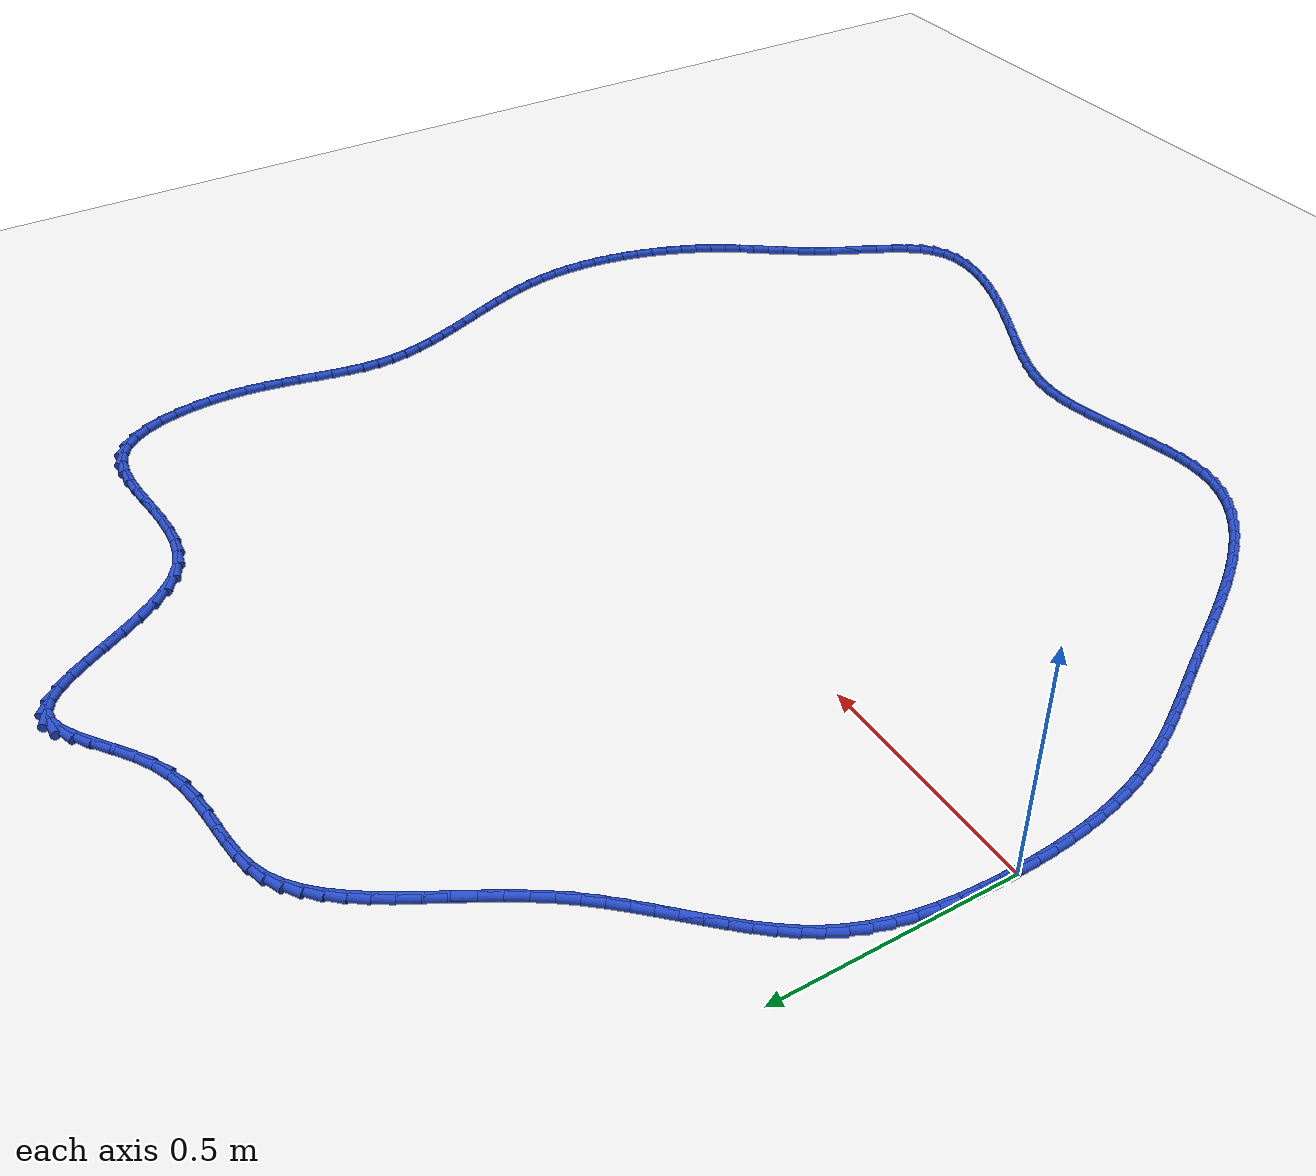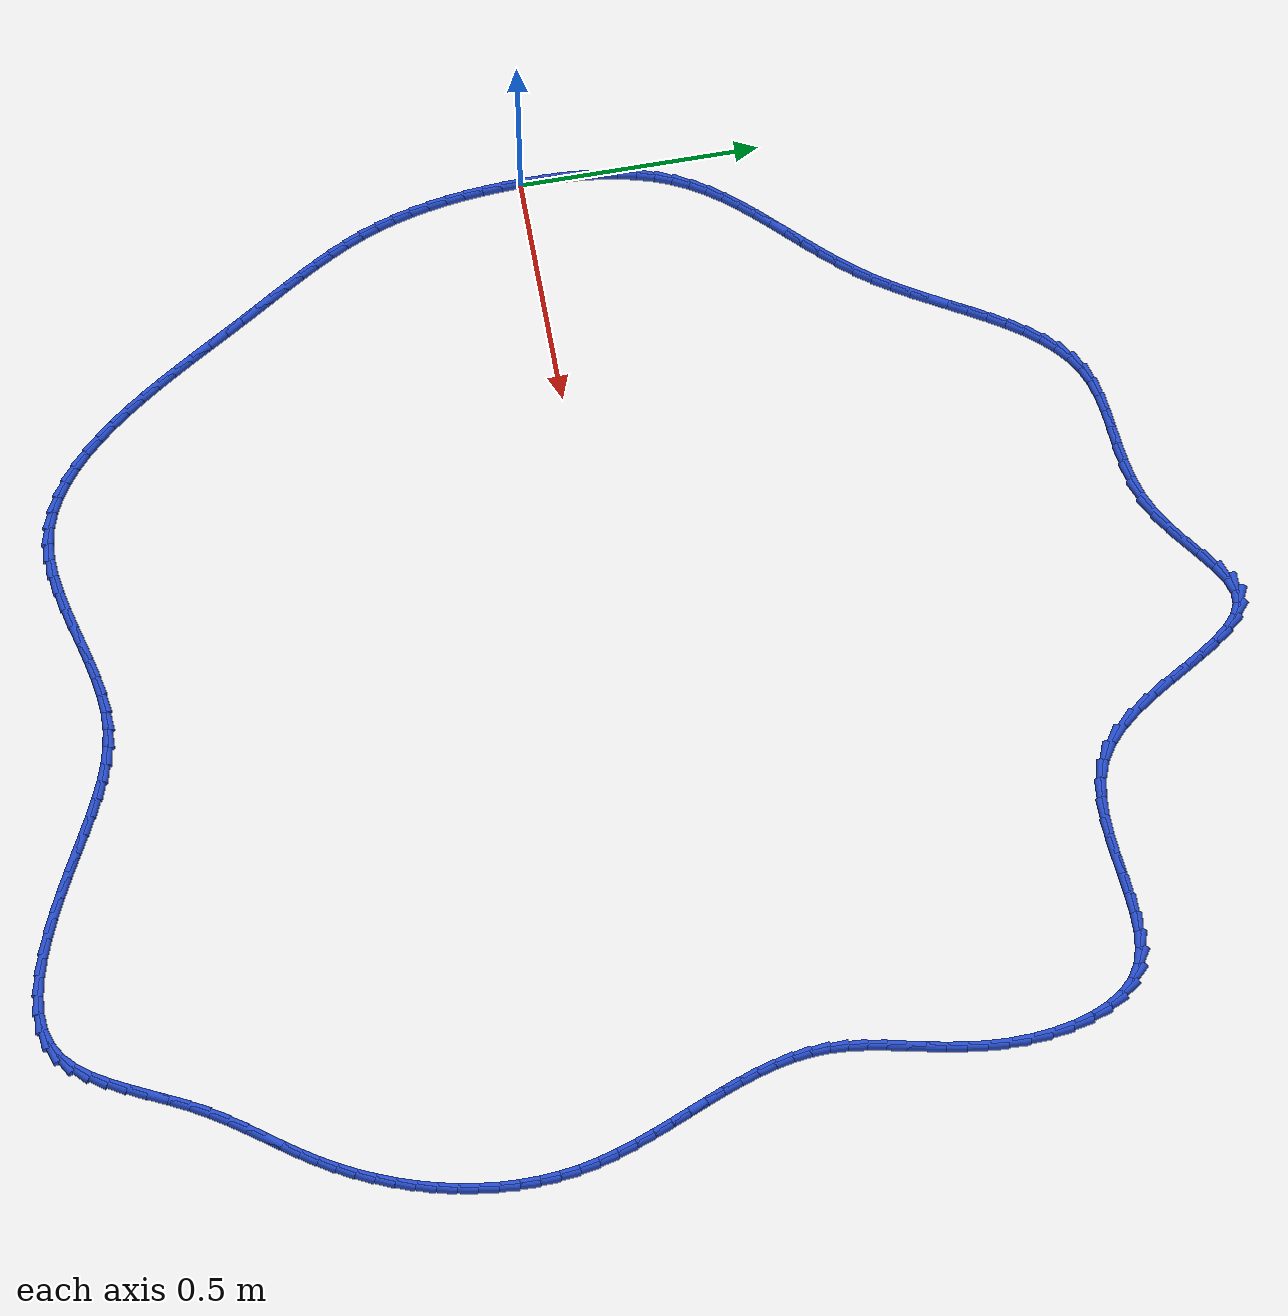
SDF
<sdf version="1.6">
 <world name="default">
  <light name="sun" type="directional">
   <pose>0 0 10 0 -0 0</pose>
   <diffuse>0.8 0.8 0.8 1</diffuse>
   <specular>0.2 0.2 0.2 1</specular>
   <attenuation>
    <range>1000</range>
    <constant>0.9</constant>
    <linear>0.01</linear>
    <quadratic>0.001</quadratic>
   </attenuation>
   <direction>-0.5 0.1 -0.9</direction>
  </light>
  <model name="ground_plane">
   <static>1</static>
   <link name="link">
    <collision name="collision">
     <geometry><plane><normal>0 0 1</normal><size>100 100</size></plane></geometry>
     <surface><friction><ode><mu>100</mu><mu2>50</mu2></ode></friction></surface>
    </collision>
    <visual name="visual">
     <cast_shadows>0</cast_shadows>
     <geometry><plane><normal>0 0 1</normal><size>100 100</size></plane></geometry>
     <material>
      <script><uri>file://media/materials/scripts/gazebo.material</uri><name>Gazebo/WhiteGlow</name></script>
     </material>
    </visual>
   </link>
  </model>
  <gravity>0 0 -9.8</gravity>
  <magnetic_field>6e-06 2.3e-05 -4.2e-05</magnetic_field>
  <atmosphere type="adiabatic"/>
  <physics name="default_physics" default="0" type="ode">
   <max_step_size>0.001</max_step_size>
   <real_time_factor>1</real_time_factor>
   <real_time_update_rate>1000</real_time_update_rate>
  </physics>
  <scene><ambient>0.4 0.4 0.4 1</ambient><background>0.7 0.7 0.7 1</background><shadows>1</shadows></scene>
  <spherical_coordinates>
   <surface_model>EARTH_WGS84</surface_model>
   <latitude_deg>0</latitude_deg>
   <longitude_deg>0</longitude_deg>
   <elevation>0</elevation>
   <heading_deg>0</heading_deg>
  </spherical_coordinates>
  <model name="line">
   <link name="link_0">
    <pose>7.37257477290143e-18 -1.1102230246251565e-16 0.01 0 1.57 -1.564874342488282</pose>
    <collision name="collision">
     <geometry><cylinder><radius>0.01</radius><length>0.08</length></cylinder></geometry>
    </collision>
    <visual name="visual">
     <material>
      <script><name>Gazebo/Blue</name><uri>file://media/materials/scripts/gazebo.material</uri></script>
     </material>
     <geometry><cylinder><radius>0.01</radius><length>0.08</length></cylinder></geometry>
    </visual>
   </link>
   <link name="link_1">
    <pose>-0.00024126828564227624 0.040740645825106704 0.01 0 1.57 1.5445311652463174</pose>
    <collision name="collision">
     <geometry><cylinder><radius>0.01</radius><length>0.08</length></cylinder></geometry>
    </collision>
    <visual name="visual">
     <material>
      <script><name>Gazebo/Blue</name><uri>file://media/materials/scripts/gazebo.material</uri></script>
     </material>
     <geometry><cylinder><radius>0.01</radius><length>0.08</length></cylinder></geometry>
    </visual>
   </link>
   <link name="link_2">
    <pose>0.0008283967256588699 0.08145690128900905 0.01 0 1.57 1.5062413362161842</pose>
    <collision name="collision">
     <geometry><cylinder><radius>0.01</radius><length>0.08</length></cylinder></geometry>
    </collision>
    <visual name="visual">
     <material>
      <script><name>Gazebo/Blue</name><uri>file://media/materials/scripts/gazebo.material</uri></script>
     </material>
     <geometry><cylinder><radius>0.01</radius><length>0.08</length></cylinder></geometry>
    </visual>
   </link>
   <link name="link_3">
    <pose>0.003442619523283141 0.12189669234528841 0.01 0 1.57 1.4611831468869003</pose>
    <collision name="collision">
     <geometry><cylinder><radius>0.01</radius><length>0.08</length></cylinder></geometry>
    </collision>
    <visual name="visual">
     <material>
      <script><name>Gazebo/Blue</name><uri>file://media/materials/scripts/gazebo.material</uri></script>
     </material>
     <geometry><cylinder><radius>0.01</radius><length>0.08</length></cylinder></geometry>
    </visual>
   </link>
   <link name="link_4">
    <pose>0.007835024596610226 0.16180794494752615 0.01 0 1.57 1.4085722016254905</pose>
    <collision name="collision">
     <geometry><cylinder><radius>0.01</radius><length>0.08</length></cylinder></geometry>
    </collision>
    <visual name="visual">
     <material>
      <script><name>Gazebo/Blue</name><uri>file://media/materials/scripts/gazebo.material</uri></script>
     </material>
     <geometry><cylinder><radius>0.01</radius><length>0.08</length></cylinder></geometry>
    </visual>
   </link>
   <link name="link_5">
    <pose>0.014239236435019828 0.20093858504930384 0.01 0 1.57 1.3475439360149963</pose>
    <collision name="collision">
     <geometry><cylinder><radius>0.01</radius><length>0.08</length></cylinder></geometry>
    </collision>
    <visual name="visual">
     <material>
      <script><name>Gazebo/Blue</name><uri>file://media/materials/scripts/gazebo.material</uri></script>
     </material>
     <geometry><cylinder><radius>0.01</radius><length>0.08</length></cylinder></geometry>
    </visual>
   </link>
   <link name="link_6">
    <pose>0.02288887952789164 0.23903653860420296 0.01 0 1.57 1.2772290212839037</pose>
    <collision name="collision">
     <geometry><cylinder><radius>0.01</radius><length>0.08</length></cylinder></geometry>
    </collision>
    <visual name="visual">
     <material>
      <script><name>Gazebo/Blue</name><uri>file://media/materials/scripts/gazebo.material</uri></script>
     </material>
     <geometry><cylinder><radius>0.01</radius><length>0.08</length></cylinder></geometry>
    </visual>
   </link>
   <link name="link_7">
    <pose>0.03401757836460534 0.2758497315658047 0.01 0 1.57 1.1968849304573805</pose>
    <collision name="collision">
     <geometry><cylinder><radius>0.01</radius><length>0.08</length></cylinder></geometry>
    </collision>
    <visual name="visual">
     <material>
      <script><name>Gazebo/Blue</name><uri>file://media/materials/scripts/gazebo.material</uri></script>
     </material>
     <geometry><cylinder><radius>0.01</radius><length>0.08</length></cylinder></geometry>
    </visual>
   </link>
   <link name="link_8">
    <pose>0.04785895743454065 0.31112608988769097 0.01 0 1.57 1.1069030191502465</pose>
    <collision name="collision">
     <geometry><cylinder><radius>0.01</radius><length>0.08</length></cylinder></geometry>
    </collision>
    <visual name="visual">
     <material>
      <script><name>Gazebo/Blue</name><uri>file://media/materials/scripts/gazebo.material</uri></script>
     </material>
     <geometry><cylinder><radius>0.01</radius><length>0.08</length></cylinder></geometry>
    </visual>
   </link>
   <link name="link_9">
    <pose>0.0646235438690067 0.34463467769089656 0.01 0 1.57 1.0198124413094176</pose>
    <collision name="collision">
     <geometry><cylinder><radius>0.01</radius><length>0.08</length></cylinder></geometry>
    </collision>
    <visual name="visual">
     <material>
      <script><name>Gazebo/Blue</name><uri>file://media/materials/scripts/gazebo.material</uri></script>
     </material>
     <geometry><cylinder><radius>0.01</radius><length>0.08</length></cylinder></geometry>
    </visual>
   </link>
   <link name="link_10">
    <pose>0.08417829868264215 0.3764589828536429 0.01 0 1.57 0.9464721863749267</pose>
    <collision name="collision">
     <geometry><cylinder><radius>0.01</radius><length>0.08</length></cylinder></geometry>
    </collision>
    <visual name="visual">
     <material>
      <script><name>Gazebo/Blue</name><uri>file://media/materials/scripts/gazebo.material</uri></script>
     </material>
     <geometry><cylinder><radius>0.01</radius><length>0.08</length></cylinder></geometry>
    </visual>
   </link>
   <link name="link_11">
    <pose>0.1061267438887049 0.4069235865301882 0.01 0 1.57 0.8880197006408748</pose>
    <collision name="collision">
     <geometry><cylinder><radius>0.01</radius><length>0.08</length></cylinder></geometry>
    </collision>
    <visual name="visual">
     <material>
      <script><name>Gazebo/Blue</name><uri>file://media/materials/scripts/gazebo.material</uri></script>
     </material>
     <geometry><cylinder><radius>0.01</radius><length>0.08</length></cylinder></geometry>
    </visual>
   </link>
   <link name="link_12">
    <pose>0.1300656846701461 0.4363592169624078 0.01 0 1.57 0.8445059594094365</pose>
    <collision name="collision">
     <geometry><cylinder><radius>0.01</radius><length>0.08</length></cylinder></geometry>
    </collision>
    <visual name="visual">
     <material>
      <script><name>Gazebo/Blue</name><uri>file://media/materials/scripts/gazebo.material</uri></script>
     </material>
     <geometry><cylinder><radius>0.01</radius><length>0.08</length></cylinder></geometry>
    </visual>
   </link>
   <link name="link_13">
    <pose>0.155591926209917 0.46509660239217726 0.01 0 1.57 0.8155182214624811</pose>
    <collision name="collision">
     <geometry><cylinder><radius>0.01</radius><length>0.08</length></cylinder></geometry>
    </collision>
    <visual name="visual">
     <material>
      <script><name>Gazebo/Blue</name><uri>file://media/materials/scripts/gazebo.material</uri></script>
     </material>
     <geometry><cylinder><radius>0.01</radius><length>0.08</length></cylinder></geometry>
    </visual>
   </link>
   <link name="link_14">
    <pose>0.1823022736909687 0.4934664710613719 0.01 0 1.57 0.800476850619655</pose>
    <collision name="collision">
     <geometry><cylinder><radius>0.01</radius><length>0.08</length></cylinder></geometry>
    </collision>
    <visual name="visual">
     <material>
      <script><name>Gazebo/Blue</name><uri>file://media/materials/scripts/gazebo.material</uri></script>
     </material>
     <geometry><cylinder><radius>0.01</radius><length>0.08</length></cylinder></geometry>
    </visual>
   </link>
   <link name="link_15">
    <pose>0.20979353229625253 0.521799551211867 0.01 0 1.57 0.7988150344108635</pose>
    <collision name="collision">
     <geometry><cylinder><radius>0.01</radius><length>0.08</length></cylinder></geometry>
    </collision>
    <visual name="visual">
     <material>
      <script><name>Gazebo/Blue</name><uri>file://media/materials/scripts/gazebo.material</uri></script>
     </material>
     <geometry><cylinder><radius>0.01</radius><length>0.08</length></cylinder></geometry>
    </visual>
   </link>
   <link name="link_16">
    <pose>0.23766250720871962 0.5504265710855382 0.01 0 1.57 0.8100570907721972</pose>
    <collision name="collision">
     <geometry><cylinder><radius>0.01</radius><length>0.08</length></cylinder></geometry>
    </collision>
    <visual name="visual">
     <material>
      <script><name>Gazebo/Blue</name><uri>file://media/materials/scripts/gazebo.material</uri></script>
     </material>
     <geometry><cylinder><radius>0.01</radius><length>0.08</length></cylinder></geometry>
    </visual>
   </link>
   <link name="link_17">
    <pose>0.2655060036113212 0.5796782589242607 0.01 0 1.57 0.8338186093596895</pose>
    <collision name="collision">
     <geometry><cylinder><radius>0.01</radius><length>0.08</length></cylinder></geometry>
    </collision>
    <visual name="visual">
     <material>
      <script><name>Gazebo/Blue</name><uri>file://media/materials/scripts/gazebo.material</uri></script>
     </material>
     <geometry><cylinder><radius>0.01</radius><length>0.08</length></cylinder></geometry>
    </visual>
   </link>
   <link name="link_18">
    <pose>0.29292082668700836 0.6098853429699098 0.01 0 1.57 0.869746077668454</pose>
    <collision name="collision">
     <geometry><cylinder><radius>0.01</radius><length>0.08</length></cylinder></geometry>
    </collision>
    <visual name="visual">
     <material>
      <script><name>Gazebo/Blue</name><uri>file://media/materials/scripts/gazebo.material</uri></script>
     </material>
     <geometry><cylinder><radius>0.01</radius><length>0.08</length></cylinder></geometry>
    </visual>
   </link>
   <link name="link_19">
    <pose>0.31950378161873233 0.6413785514643608 0.01 0 1.57 0.9174079820426917</pose>
    <collision name="collision">
     <geometry><cylinder><radius>0.01</radius><length>0.08</length></cylinder></geometry>
    </collision>
    <visual name="visual">
     <material>
      <script><name>Gazebo/Blue</name><uri>file://media/materials/scripts/gazebo.material</uri></script>
     </material>
     <geometry><cylinder><radius>0.01</radius><length>0.08</length></cylinder></geometry>
    </visual>
   </link>
   <link name="link_20">
    <pose>0.3448516752477059 0.6744886106825727 0.01 0 1.57 0.9713655664704544</pose>
    <collision name="collision">
     <geometry><cylinder><radius>0.01</radius><length>0.08</length></cylinder></geometry>
    </collision>
    <visual name="visual">
     <material>
      <script><name>Gazebo/Blue</name><uri>file://media/materials/scripts/gazebo.material</uri></script>
     </material>
     <geometry><cylinder><radius>0.01</radius><length>0.08</length></cylinder></geometry>
    </visual>
   </link>
   <link name="link_21">
    <pose>0.36869680018552614 0.7093855429359073 0.01 0 1.57 1.0137798763475485</pose>
    <collision name="collision">
     <geometry><cylinder><radius>0.01</radius><length>0.08</length></cylinder></geometry>
    </collision>
    <visual name="visual">
     <material>
      <script><name>Gazebo/Blue</name><uri>file://media/materials/scripts/gazebo.material</uri></script>
     </material>
     <geometry><cylinder><radius>0.01</radius><length>0.08</length></cylinder></geometry>
    </visual>
   </link>
   <link name="link_22">
    <pose>0.39127638939382337 0.745640444793188 0.01 0 1.57 1.0415218999347804</pose>
    <collision name="collision">
     <geometry><cylinder><radius>0.01</radius><length>0.08</length></cylinder></geometry>
    </collision>
    <visual name="visual">
     <material>
      <script><name>Gazebo/Blue</name><uri>file://media/materials/scripts/gazebo.material</uri></script>
     </material>
     <geometry><cylinder><radius>0.01</radius><length>0.08</length></cylinder></geometry>
    </visual>
   </link>
   <link name="link_23">
    <pose>0.4129452838079878 0.7826849142804755 0.01 0 1.57 1.055331672748383</pose>
    <collision name="collision">
     <geometry><cylinder><radius>0.01</radius><length>0.08</length></cylinder></geometry>
    </collision>
    <visual name="visual">
     <material>
      <script><name>Gazebo/Blue</name><uri>file://media/materials/scripts/gazebo.material</uri></script>
     </material>
     <geometry><cylinder><radius>0.01</radius><length>0.08</length></cylinder></geometry>
    </visual>
   </link>
   <link name="link_24">
    <pose>0.43405832436340974 0.81995054942383 0.01 0 1.57 1.0554195280509582</pose>
    <collision name="collision">
     <geometry><cylinder><radius>0.01</radius><length>0.08</length></cylinder></geometry>
    </collision>
    <visual name="visual">
     <material>
      <script><name>Gazebo/Blue</name><uri>file://media/materials/scripts/gazebo.material</uri></script>
     </material>
     <geometry><cylinder><radius>0.01</radius><length>0.08</length></cylinder></geometry>
    </visual>
   </link>
   <link name="link_25">
    <pose>0.454970351995479 0.8568689482493117 0.01 0 1.57 1.0413915050004514</pose>
    <collision name="collision">
     <geometry><cylinder><radius>0.01</radius><length>0.08</length></cylinder></geometry>
    </collision>
    <visual name="visual">
     <material>
      <script><name>Gazebo/Blue</name><uri>file://media/materials/scripts/gazebo.material</uri></script>
     </material>
     <geometry><cylinder><radius>0.01</radius><length>0.08</length></cylinder></geometry>
    </visual>
   </link>
   <link name="link_26">
    <pose>0.4760362076395862 0.8928717087829808 0.01 0 1.57 1.0121902530101687</pose>
    <collision name="collision">
     <geometry><cylinder><radius>0.01</radius><length>0.08</length></cylinder></geometry>
    </collision>
    <visual name="visual">
     <material>
      <script><name>Gazebo/Blue</name><uri>file://media/materials/scripts/gazebo.material</uri></script>
     </material>
     <geometry><cylinder><radius>0.01</radius><length>0.08</length></cylinder></geometry>
    </visual>
   </link>
   <link name="link_27">
    <pose>0.49761073223112107 0.9273904290508974 0.01 0 1.57 0.9660562318140632</pose>
    <collision name="collision">
     <geometry><cylinder><radius>0.01</radius><length>0.08</length></cylinder></geometry>
    </collision>
    <visual name="visual">
     <material>
      <script><name>Gazebo/Blue</name><uri>file://media/materials/scripts/gazebo.material</uri></script>
     </material>
     <geometry><cylinder><radius>0.01</radius><length>0.08</length></cylinder></geometry>
    </visual>
   </link>
   <link name="link_28">
    <pose>0.5200487667054741 0.959856707079122 0.01 0 1.57 0.9005654896153721</pose>
    <collision name="collision">
     <geometry><cylinder><radius>0.01</radius><length>0.08</length></cylinder></geometry>
    </collision>
    <visual name="visual">
     <material>
      <script><name>Gazebo/Blue</name><uri>file://media/materials/scripts/gazebo.material</uri></script>
     </material>
     <geometry><cylinder><radius>0.01</radius><length>0.08</length></cylinder></geometry>
    </visual>
   </link>
   <link name="link_29">
    <pose>0.5437051519980354 0.989702140893715 0.01 0 1.57 0.8128864591380504</pose>
    <collision name="collision">
     <geometry><cylinder><radius>0.01</radius><length>0.08</length></cylinder></geometry>
    </collision>
    <visual name="visual">
     <material>
      <script><name>Gazebo/Blue</name><uri>file://media/materials/scripts/gazebo.material</uri></script>
     </material>
     <geometry><cylinder><radius>0.01</radius><length>0.08</length></cylinder></geometry>
    </visual>
   </link>
   <link name="link_30">
    <pose>0.5689347290441951 1.0163583285207363 0.01 0 1.57 0.7005167500098161</pose>
    <collision name="collision">
     <geometry><cylinder><radius>0.01</radius><length>0.08</length></cylinder></geometry>
    </collision>
    <visual name="visual">
     <material>
      <script><name>Gazebo/Blue</name><uri>file://media/materials/scripts/gazebo.material</uri></script>
     </material>
     <geometry><cylinder><radius>0.01</radius><length>0.08</length></cylinder></geometry>
    </visual>
   </link>
   <link name="link_31">
    <pose>0.5960923387793435 1.0392568679862462 0.01 0 1.57 0.5627940387736703</pose>
    <collision name="collision">
     <geometry><cylinder><radius>0.01</radius><length>0.08</length></cylinder></geometry>
    </collision>
    <visual name="visual">
     <material>
      <script><name>Gazebo/Blue</name><uri>file://media/materials/scripts/gazebo.material</uri></script>
     </material>
     <geometry><cylinder><radius>0.01</radius><length>0.08</length></cylinder></geometry>
    </visual>
   </link>
   <link name="link_32">
    <pose>0.6255328221388703 1.0578293573163047 0.01 0 1.57 0.4038892538528162</pose>
    <collision name="collision">
     <geometry><cylinder><radius>0.01</radius><length>0.08</length></cylinder></geometry>
    </collision>
    <visual name="visual">
     <material>
      <script><name>Gazebo/Blue</name><uri>file://media/materials/scripts/gazebo.material</uri></script>
     </material>
     <geometry><cylinder><radius>0.01</radius><length>0.08</length></cylinder></geometry>
    </visual>
   </link>
   <link name="link_33">
    <pose>0.6575995567666834 1.0715342072497898 0.01 0 1.57 0.2583672371982367</pose>
    <collision name="collision">
     <geometry><cylinder><radius>0.01</radius><length>0.08</length></cylinder></geometry>
    </collision>
    <visual name="visual">
     <material>
      <script><name>Gazebo/Blue</name><uri>file://media/materials/scripts/gazebo.material</uri></script>
     </material>
     <geometry><cylinder><radius>0.01</radius><length>0.08</length></cylinder></geometry>
    </visual>
   </link>
   <link name="link_34">
    <pose>0.6922657802741444 1.0806955884523786 0.01 0 1.57 0.16094464935645597</pose>
    <collision name="collision">
     <geometry><cylinder><radius>0.01</radius><length>0.08</length></cylinder></geometry>
    </collision>
    <visual name="visual">
     <material>
      <script><name>Gazebo/Blue</name><uri>file://media/materials/scripts/gazebo.material</uri></script>
     </material>
     <geometry><cylinder><radius>0.01</radius><length>0.08</length></cylinder></geometry>
    </visual>
   </link>
   <link name="link_35">
    <pose>0.7290635222869535 1.0866696599178962 0.01 0 1.57 0.10892706521384078</pose>
    <collision name="collision">
     <geometry><cylinder><radius>0.01</radius><length>0.08</length></cylinder></geometry>
    </collision>
    <visual name="visual">
     <material>
      <script><name>Gazebo/Blue</name><uri>file://media/materials/scripts/gazebo.material</uri></script>
     </material>
     <geometry><cylinder><radius>0.01</radius><length>0.08</length></cylinder></geometry>
    </visual>
   </link>
   <link name="link_36">
    <pose>0.7674989979613372 1.0908729608510006 0.01 0 1.57 0.09694440888248296</pose>
    <collision name="collision">
     <geometry><cylinder><radius>0.01</radius><length>0.08</length></cylinder></geometry>
    </collision>
    <visual name="visual">
     <material>
      <script><name>Gazebo/Blue</name><uri>file://media/materials/scripts/gazebo.material</uri></script>
     </material>
     <geometry><cylinder><radius>0.01</radius><length>0.08</length></cylinder></geometry>
    </visual>
   </link>
   <link name="link_37">
    <pose>0.8070784224535215 1.0947220304563503 0.01 0 1.57 0.12148254916971234</pose>
    <collision name="collision">
     <geometry><cylinder><radius>0.01</radius><length>0.08</length></cylinder></geometry>
    </collision>
    <visual name="visual">
     <material>
      <script><name>Gazebo/Blue</name><uri>file://media/materials/scripts/gazebo.material</uri></script>
     </material>
     <geometry><cylinder><radius>0.01</radius><length>0.08</length></cylinder></geometry>
    </visual>
   </link>
   <link name="link_38">
    <pose>0.8473080109197331 1.0996334079386034 0.01 0 1.57 0.1809874980426755</pose>
    <collision name="collision">
     <geometry><cylinder><radius>0.01</radius><length>0.08</length></cylinder></geometry>
    </collision>
    <visual name="visual">
     <material>
      <script><name>Gazebo/Blue</name><uri>file://media/materials/scripts/gazebo.material</uri></script>
     </material>
     <geometry><cylinder><radius>0.01</radius><length>0.08</length></cylinder></geometry>
    </visual>
   </link>
   <link name="link_39">
    <pose>0.8876939785161979 1.107023632502418 0.01 0 1.57 0.2746753520392098</pose>
    <collision name="collision">
     <geometry><cylinder><radius>0.01</radius><length>0.08</length></cylinder></geometry>
    </collision>
    <visual name="visual">
     <material>
      <script><name>Gazebo/Blue</name><uri>file://media/materials/scripts/gazebo.material</uri></script>
     </material>
     <geometry><cylinder><radius>0.01</radius><length>0.08</length></cylinder></geometry>
    </visual>
   </link>
   <link name="link_40">
    <pose>0.9277425403991421 1.118309243352452 0.01 0 1.57 0.4003471819447287</pose>
    <collision name="collision">
     <geometry><cylinder><radius>0.01</radius><length>0.08</length></cylinder></geometry>
    </collision>
    <visual name="visual">
     <material>
      <script><name>Gazebo/Blue</name><uri>file://media/materials/scripts/gazebo.material</uri></script>
     </material>
     <geometry><cylinder><radius>0.01</radius><length>0.08</length></cylinder></geometry>
    </visual>
   </link>
   <link name="link_41">
    <pose>0.9669599629667047 1.1349061554492776 0.01 0 1.57 0.532530980872771</pose>
    <collision name="collision">
     <geometry><cylinder><radius>0.01</radius><length>0.08</length></cylinder></geometry>
    </collision>
    <visual name="visual">
     <material>
      <script><name>Gazebo/Blue</name><uri>file://media/materials/scripts/gazebo.material</uri></script>
     </material>
     <geometry><cylinder><radius>0.01</radius><length>0.08</length></cylinder></geometry>
    </visual>
   </link>
   <link name="link_42">
    <pose>1.0049302801953897 1.1572828961802586 0.01 0 1.57 0.6142302126609227</pose>
    <collision name="collision">
     <geometry><cylinder><radius>0.01</radius><length>0.08</length></cylinder></geometry>
    </collision>
    <visual name="visual">
     <material>
      <script><name>Gazebo/Blue</name><uri>file://media/materials/scripts/gazebo.material</uri></script>
     </material>
     <geometry><cylinder><radius>0.01</radius><length>0.08</length></cylinder></geometry>
    </visual>
   </link>
   <link name="link_43">
    <pose>1.0414718600117672 1.1830532676483139 0.01 0 1.57 0.6437002070872572</pose>
    <collision name="collision">
     <geometry><cylinder><radius>0.01</radius><length>0.08</length></cylinder></geometry>
    </collision>
    <visual name="visual">
     <material>
      <script><name>Gazebo/Blue</name><uri>file://media/materials/scripts/gazebo.material</uri></script>
     </material>
     <geometry><cylinder><radius>0.01</radius><length>0.08</length></cylinder></geometry>
    </visual>
   </link>
   <link name="link_44">
    <pose>1.0764470311765433 1.2092955281109161 0.01 0 1.57 0.6207934460507247</pose>
    <collision name="collision">
     <geometry><cylinder><radius>0.01</radius><length>0.08</length></cylinder></geometry>
    </collision>
    <visual name="visual">
     <material>
      <script><name>Gazebo/Blue</name><uri>file://media/materials/scripts/gazebo.material</uri></script>
     </material>
     <geometry><cylinder><radius>0.01</radius><length>0.08</length></cylinder></geometry>
    </visual>
   </link>
   <link name="link_45">
    <pose>1.1097181224504251 1.233087935825537 0.01 0 1.57 0.530138034267043</pose>
    <collision name="collision">
     <geometry><cylinder><radius>0.01</radius><length>0.08</length></cylinder></geometry>
    </collision>
    <visual name="visual">
     <material>
      <script><name>Gazebo/Blue</name><uri>file://media/materials/scripts/gazebo.material</uri></script>
     </material>
     <geometry><cylinder><radius>0.01</radius><length>0.08</length></cylinder></geometry>
    </visual>
   </link>
   <link name="link_46">
    <pose>1.1411474625941191 1.2515087490496493 0.01 0 1.57 0.3312195994265492</pose>
    <collision name="collision">
     <geometry><cylinder><radius>0.01</radius><length>0.08</length></cylinder></geometry>
    </collision>
    <visual name="visual">
     <material>
      <script><name>Gazebo/Blue</name><uri>file://media/materials/scripts/gazebo.material</uri></script>
     </material>
     <geometry><cylinder><radius>0.01</radius><length>0.08</length></cylinder></geometry>
    </visual>
   </link>
   <link name="link_47">
    <pose>1.1705973803683316 1.2616362260407246 0.01 0 1.57 -0.03236546962473143</pose>
    <collision name="collision">
     <geometry><cylinder><radius>0.01</radius><length>0.08</length></cylinder></geometry>
    </collision>
    <visual name="visual">
     <material>
      <script><name>Gazebo/Blue</name><uri>file://media/materials/scripts/gazebo.material</uri></script>
     </material>
     <geometry><cylinder><radius>0.01</radius><length>0.08</length></cylinder></geometry>
    </visual>
   </link>
   <link name="link_48">
    <pose>1.1979571117771861 1.2607504061575165 0.01 0 1.57 -0.4384120962369894</pose>
    <collision name="collision">
     <geometry><cylinder><radius>0.01</radius><length>0.08</length></cylinder></geometry>
    </collision>
    <visual name="visual">
     <material>
      <script><name>Gazebo/Blue</name><uri>file://media/materials/scripts/gazebo.material</uri></script>
     </material>
     <geometry><cylinder><radius>0.01</radius><length>0.08</length></cylinder></geometry>
    </visual>
   </link>
   <link name="link_49">
    <pose>1.223470258809501 1.248788767781534 0.01 0 1.57 -0.7208110931500036</pose>
    <collision name="collision">
     <geometry><cylinder><radius>0.01</radius><length>0.08</length></cylinder></geometry>
    </collision>
    <visual name="visual">
     <material>
      <script><name>Gazebo/Blue</name><uri>file://media/materials/scripts/gazebo.material</uri></script>
     </material>
     <geometry><cylinder><radius>0.01</radius><length>0.08</length></cylinder></geometry>
    </visual>
   </link>
   <link name="link_50">
    <pose>1.2476304705166859 1.227563926441597 0.01 0 1.57 -0.887652762361453</pose>
    <collision name="collision">
     <geometry><cylinder><radius>0.01</radius><length>0.08</length></cylinder></geometry>
    </collision>
    <visual name="visual">
     <material>
      <script><name>Gazebo/Blue</name><uri>file://media/materials/scripts/gazebo.material</uri></script>
     </material>
     <geometry><cylinder><radius>0.01</radius><length>0.08</length></cylinder></geometry>
    </visual>
   </link>
   <link name="link_51">
    <pose>1.2709366409798193 1.1989278308619362 0.01 0 1.57 -0.9796805731014854</pose>
    <collision name="collision">
     <geometry><cylinder><radius>0.01</radius><length>0.08</length></cylinder></geometry>
    </collision>
    <visual name="visual">
     <material>
      <script><name>Gazebo/Blue</name><uri>file://media/materials/scripts/gazebo.material</uri></script>
     </material>
     <geometry><cylinder><radius>0.01</radius><length>0.08</length></cylinder></geometry>
    </visual>
   </link>
   <link name="link_52">
    <pose>1.2938876642799808 1.164732429766782 0.01 0 1.57 -1.0235547129125873</pose>
    <collision name="collision">
     <geometry><cylinder><radius>0.01</radius><length>0.08</length></cylinder></geometry>
    </collision>
    <visual name="visual">
     <material>
      <script><name>Gazebo/Blue</name><uri>file://media/materials/scripts/gazebo.material</uri></script>
     </material>
     <geometry><cylinder><radius>0.01</radius><length>0.08</length></cylinder></geometry>
    </visual>
   </link>
   <link name="link_53">
    <pose>1.3169824344982497 1.1268296718803652 0.01 0 1.57 -1.0325525086766996</pose>
    <collision name="collision">
     <geometry><cylinder><radius>0.01</radius><length>0.08</length></cylinder></geometry>
    </collision>
    <visual name="visual">
     <material>
      <script><name>Gazebo/Blue</name><uri>file://media/materials/scripts/gazebo.material</uri></script>
     </material>
     <geometry><cylinder><radius>0.01</radius><length>0.08</length></cylinder></geometry>
    </visual>
   </link>
   <link name="link_54">
    <pose>1.340719845715705 1.0870715059269145 0.01 0 1.57 -1.0116920395291449</pose>
    <collision name="collision">
     <geometry><cylinder><radius>0.01</radius><length>0.08</length></cylinder></geometry>
    </collision>
    <visual name="visual">
     <material>
      <script><name>Gazebo/Blue</name><uri>file://media/materials/scripts/gazebo.material</uri></script>
     </material>
     <geometry><cylinder><radius>0.01</radius><length>0.08</length></cylinder></geometry>
    </visual>
   </link>
   <link name="link_55">
    <pose>1.3655987920134263 1.0473098806306613 0.01 0 1.57 -0.9604212979409047</pose>
    <collision name="collision">
     <geometry><cylinder><radius>0.01</radius><length>0.08</length></cylinder></geometry>
    </collision>
    <visual name="visual">
     <material>
      <script><name>Gazebo/Blue</name><uri>file://media/materials/scripts/gazebo.material</uri></script>
     </material>
     <geometry><cylinder><radius>0.01</radius><length>0.08</length></cylinder></geometry>
    </visual>
   </link>
   <link name="link_56">
    <pose>1.392118167472492 1.009396744715836 0.01 0 1.57 -0.8735084850807119</pose>
    <collision name="collision">
     <geometry><cylinder><radius>0.01</radius><length>0.08</length></cylinder></geometry>
    </collision>
    <visual name="visual">
     <material>
      <script><name>Gazebo/Blue</name><uri>file://media/materials/scripts/gazebo.material</uri></script>
     </material>
     <geometry><cylinder><radius>0.01</radius><length>0.08</length></cylinder></geometry>
    </visual>
   </link>
   <link name="link_57">
    <pose>1.4207768661739821 0.975184046906668 0.01 0 1.57 -0.741451710092847</pose>
    <collision name="collision">
     <geometry><cylinder><radius>0.01</radius><length>0.08</length></cylinder></geometry>
    </collision>
    <visual name="visual">
     <material>
      <script><name>Gazebo/Blue</name><uri>file://media/materials/scripts/gazebo.material</uri></script>
     </material>
     <geometry><cylinder><radius>0.01</radius><length>0.08</length></cylinder></geometry>
    </visual>
   </link>
   <link name="link_58">
    <pose>1.4520737821989762 0.9465237359273885 0.01 0 1.57 -0.5548622052966526</pose>
    <collision name="collision">
     <geometry><cylinder><radius>0.01</radius><length>0.08</length></cylinder></geometry>
    </collision>
    <visual name="visual">
     <material>
      <script><name>Gazebo/Blue</name><uri>file://media/materials/scripts/gazebo.material</uri></script>
     </material>
     <geometry><cylinder><radius>0.01</radius><length>0.08</length></cylinder></geometry>
    </visual>
   </link>
   <link name="link_59">
    <pose>1.4864823347995044 0.9251967931378107 0.01 0 1.57 -0.3521727831574931</pose>
    <collision name="collision">
     <geometry><cylinder><radius>0.01</radius><length>0.08</length></cylinder></geometry>
    </collision>
    <visual name="visual">
     <material>
      <script><name>Gazebo/Blue</name><uri>file://media/materials/scripts/gazebo.material</uri></script>
     </material>
     <geometry><cylinder><radius>0.01</radius><length>0.08</length></cylinder></geometry>
    </visual>
   </link>
   <link name="link_60">
    <pose>1.523921033934629 0.911438342614883 0.01 0 1.57 -0.18492250126478751</pose>
    <collision name="collision">
     <geometry><cylinder><radius>0.01</radius><length>0.08</length></cylinder></geometry>
    </collision>
    <visual name="visual">
     <material>
      <script><name>Gazebo/Blue</name><uri>file://media/materials/scripts/gazebo.material</uri></script>
     </material>
     <geometry><cylinder><radius>0.01</radius><length>0.08</length></cylinder></geometry>
    </visual>
   </link>
   <link name="link_61">
    <pose>1.5637701810564568 0.903984175930749 0.01 0 1.57 -0.059417820040100336</pose>
    <collision name="collision">
     <geometry><cylinder><radius>0.01</radius><length>0.08</length></cylinder></geometry>
    </collision>
    <visual name="visual">
     <material>
      <script><name>Gazebo/Blue</name><uri>file://media/materials/scripts/gazebo.material</uri></script>
     </material>
     <geometry><cylinder><radius>0.01</radius><length>0.08</length></cylinder></geometry>
    </visual>
   </link>
   <link name="link_62">
    <pose>1.6053879439230734 0.9015084249727444 0.01 0 1.57 0.027523966733935982</pose>
    <collision name="collision">
     <geometry><cylinder><radius>0.01</radius><length>0.08</length></cylinder></geometry>
    </collision>
    <visual name="visual">
     <material>
      <script><name>Gazebo/Blue</name><uri>file://media/materials/scripts/gazebo.material</uri></script>
     </material>
     <geometry><cylinder><radius>0.01</radius><length>0.08</length></cylinder></geometry>
    </visual>
   </link>
   <link name="link_63">
    <pose>1.6481324902925651 0.9026852216282066 0.01 0 1.57 0.08086690968873678</pose>
    <collision name="collision">
     <geometry><cylinder><radius>0.01</radius><length>0.08</length></cylinder></geometry>
    </collision>
    <visual name="visual">
     <material>
      <script><name>Gazebo/Blue</name><uri>file://media/materials/scripts/gazebo.material</uri></script>
     </material>
     <geometry><cylinder><radius>0.01</radius><length>0.08</length></cylinder></geometry>
    </visual>
   </link>
   <link name="link_64">
    <pose>1.691361987923018 0.906188697784472 0.01 0 1.57 0.10419555385461013</pose>
    <collision name="collision">
     <geometry><cylinder><radius>0.01</radius><length>0.08</length></cylinder></geometry>
    </collision>
    <visual name="visual">
     <material>
      <script><name>Gazebo/Blue</name><uri>file://media/materials/scripts/gazebo.material</uri></script>
     </material>
     <geometry><cylinder><radius>0.01</radius><length>0.08</length></cylinder></geometry>
    </visual>
   </link>
   <link name="link_65">
    <pose>1.7344346045725179 0.9106929853288773 0.01 0 1.57 0.09854057936121084</pose>
    <collision name="collision">
     <geometry><cylinder><radius>0.01</radius><length>0.08</length></cylinder></geometry>
    </collision>
    <visual name="visual">
     <material>
      <script><name>Gazebo/Blue</name><uri>file://media/materials/scripts/gazebo.material</uri></script>
     </material>
     <geometry><cylinder><radius>0.01</radius><length>0.08</length></cylinder></geometry>
    </visual>
   </link>
   <link name="link_66">
    <pose>1.7767085079991507 0.9148722161487592 0.01 0 1.57 0.061838715133478495</pose>
    <collision name="collision">
     <geometry><cylinder><radius>0.01</radius><length>0.08</length></cylinder></geometry>
    </collision>
    <visual name="visual">
     <material>
      <script><name>Gazebo/Blue</name><uri>file://media/materials/scripts/gazebo.material</uri></script>
     </material>
     <geometry><cylinder><radius>0.01</radius><length>0.08</length></cylinder></geometry>
    </visual>
   </link>
   <link name="link_67">
    <pose>1.817541865961002 0.9174005221314543 0.01 0 1.57 -0.011573047733451986</pose>
    <collision name="collision">
     <geometry><cylinder><radius>0.01</radius><length>0.08</length></cylinder></geometry>
    </collision>
    <visual name="visual">
     <material>
      <script><name>Gazebo/Blue</name><uri>file://media/materials/scripts/gazebo.material</uri></script>
     </material>
     <geometry><cylinder><radius>0.01</radius><length>0.08</length></cylinder></geometry>
    </visual>
   </link>
   <link name="link_68">
    <pose>1.8562928462161583 0.916952035164299 0.01 0 1.57 -0.13112161026357474</pose>
    <collision name="collision">
     <geometry><cylinder><radius>0.01</radius><length>0.08</length></cylinder></geometry>
    </collision>
    <visual name="visual">
     <material>
      <script><name>Gazebo/Blue</name><uri>file://media/materials/scripts/gazebo.material</uri></script>
     </material>
     <geometry><cylinder><radius>0.01</radius><length>0.08</length></cylinder></geometry>
    </visual>
   </link>
   <link name="link_69">
    <pose>1.8923196165227052 0.9122008871346304 0.01 0 1.57 -0.3077087460870319</pose>
    <collision name="collision">
     <geometry><cylinder><radius>0.01</radius><length>0.08</length></cylinder></geometry>
    </collision>
    <visual name="visual">
     <material>
      <script><name>Gazebo/Blue</name><uri>file://media/materials/scripts/gazebo.material</uri></script>
     </material>
     <geometry><cylinder><radius>0.01</radius><length>0.08</length></cylinder></geometry>
    </visual>
   </link>
   <link name="link_70">
    <pose>1.9249803446387284 0.9018212099297851 0.01 0 1.57 -0.5438525082337025</pose>
    <collision name="collision">
     <geometry><cylinder><radius>0.01</radius><length>0.08</length></cylinder></geometry>
    </collision>
    <visual name="visual">
     <material>
      <script><name>Gazebo/Blue</name><uri>file://media/materials/scripts/gazebo.material</uri></script>
     </material>
     <geometry><cylinder><radius>0.01</radius><length>0.08</length></cylinder></geometry>
    </visual>
   </link>
   <link name="link_71">
    <pose>1.9536353850999932 0.8844941217251963 0.01 0 1.57 -0.7957552287456654</pose>
    <collision name="collision">
     <geometry><cylinder><radius>0.01</radius><length>0.08</length></cylinder></geometry>
    </collision>
    <visual name="visual">
     <material>
      <script><name>Gazebo/Blue</name><uri>file://media/materials/scripts/gazebo.material</uri></script>
     </material>
     <geometry><cylinder><radius>0.01</radius><length>0.08</length></cylinder></geometry>
    </visual>
   </link>
   <link name="link_72">
    <pose>1.9779015399424775 0.8597200357419358 0.01 0 1.57 -1.0002063954576825</pose>
    <collision name="collision">
     <geometry><cylinder><radius>0.01</radius><length>0.08</length></cylinder></geometry>
    </collision>
    <visual name="visual">
     <material>
      <script><name>Gazebo/Blue</name><uri>file://media/materials/scripts/gazebo.material</uri></script>
     </material>
     <geometry><cylinder><radius>0.01</radius><length>0.08</length></cylinder></geometry>
    </visual>
   </link>
   <link name="link_73">
    <pose>1.9978893446329204 0.8285767381657223 0.01 0 1.57 -1.158053088087301</pose>
    <collision name="collision">
     <geometry><cylinder><radius>0.01</radius><length>0.08</length></cylinder></geometry>
    </collision>
    <visual name="visual">
     <material>
      <script><name>Gazebo/Blue</name><uri>file://media/materials/scripts/gazebo.material</uri></script>
     </material>
     <geometry><cylinder><radius>0.01</radius><length>0.08</length></cylinder></geometry>
    </visual>
   </link>
   <link name="link_74">
    <pose>2.013765462370057 0.7923213313101695 0.01 0 1.57 -1.2816748626171814</pose>
    <collision name="collision">
     <geometry><cylinder><radius>0.01</radius><length>0.08</length></cylinder></geometry>
    </collision>
    <visual name="visual">
     <material>
      <script><name>Gazebo/Blue</name><uri>file://media/materials/scripts/gazebo.material</uri></script>
     </material>
     <geometry><cylinder><radius>0.01</radius><length>0.08</length></cylinder></geometry>
    </visual>
   </link>
   <link name="link_75">
    <pose>2.0256965563526217 0.7522109174888914 0.01 0 1.57 -1.382172310640261</pose>
    <collision name="collision">
     <geometry><cylinder><radius>0.01</radius><length>0.08</length></cylinder></geometry>
    </collision>
    <visual name="visual">
     <material>
      <script><name>Gazebo/Blue</name><uri>file://media/materials/scripts/gazebo.material</uri></script>
     </material>
     <geometry><cylinder><radius>0.01</radius><length>0.08</length></cylinder></geometry>
    </visual>
   </link>
   <link name="link_76">
    <pose>2.0338492897793485 0.7095025990155033 0.01 0 1.57 -1.46806893944363</pose>
    <collision name="collision">
     <geometry><cylinder><radius>0.01</radius><length>0.08</length></cylinder></geometry>
    </collision>
    <visual name="visual">
     <material>
      <script><name>Gazebo/Blue</name><uri>file://media/materials/scripts/gazebo.material</uri></script>
     </material>
     <geometry><cylinder><radius>0.01</radius><length>0.08</length></cylinder></geometry>
    </visual>
   </link>
   <link name="link_77">
    <pose>2.0383903258489733 0.6654534782036178 0.01 0 1.57 -1.5459672617309674</pose>
    <collision name="collision">
     <geometry><cylinder><radius>0.01</radius><length>0.08</length></cylinder></geometry>
    </collision>
    <visual name="visual">
     <material>
      <script><name>Gazebo/Blue</name><uri>file://media/materials/scripts/gazebo.material</uri></script>
     </material>
     <geometry><cylinder><radius>0.01</radius><length>0.08</length></cylinder></geometry>
    </visual>
   </link>
   <link name="link_78">
    <pose>2.03948632776023 0.6213206573668499 0.01 0 1.57 1.5211225703982851</pose>
    <collision name="collision">
     <geometry><cylinder><radius>0.01</radius><length>0.08</length></cylinder></geometry>
    </collision>
    <visual name="visual">
     <material>
      <script><name>Gazebo/Blue</name><uri>file://media/materials/scripts/gazebo.material</uri></script>
     </material>
     <geometry><cylinder><radius>0.01</radius><length>0.08</length></cylinder></geometry>
    </visual>
   </link>
   <link name="link_79">
    <pose>2.037345700871489 0.5782623887482059 0.01 0 1.57 1.4560879660963555</pose>
    <collision name="collision">
     <geometry><cylinder><radius>0.01</radius><length>0.08</length></cylinder></geometry>
    </collision>
    <visual name="visual">
     <material>
      <script><name>Gazebo/Blue</name><uri>file://media/materials/scripts/gazebo.material</uri></script>
     </material>
     <geometry><cylinder><radius>0.01</radius><length>0.08</length></cylinder></geometry>
    </visual>
   </link>
   <link name="link_80">
    <pose>2.0325423166481733 0.536571460254334 0.01 0 1.57 1.4066875570438526</pose>
    <collision name="collision">
     <geometry><cylinder><radius>0.01</radius><length>0.08</length></cylinder></geometry>
    </collision>
    <visual name="visual">
     <material>
      <script><name>Gazebo/Blue</name><uri>file://media/materials/scripts/gazebo.material</uri></script>
     </material>
     <geometry><cylinder><radius>0.01</radius><length>0.08</length></cylinder></geometry>
    </visual>
   </link>
   <link name="link_81">
    <pose>2.0258391399916453 0.49609286553165727 0.01 0 1.57 1.3745373788478181</pose>
    <collision name="collision">
     <geometry><cylinder><radius>0.01</radius><length>0.08</length></cylinder></geometry>
    </collision>
    <visual name="visual">
     <material>
      <script><name>Gazebo/Blue</name><uri>file://media/materials/scripts/gazebo.material</uri></script>
     </material>
     <geometry><cylinder><radius>0.01</radius><length>0.08</length></cylinder></geometry>
    </visual>
   </link>
   <link name="link_82">
    <pose>2.018000726140692 0.45666783213092826 0.01 0 1.57 1.3608791147492256</pose>
    <collision name="collision">
     <geometry><cylinder><radius>0.01</radius><length>0.08</length></cylinder></geometry>
    </collision>
    <visual name="visual">
     <material>
      <script><name>Gazebo/Blue</name><uri>file://media/materials/scripts/gazebo.material</uri></script>
     </material>
     <geometry><cylinder><radius>0.01</radius><length>0.08</length></cylinder></geometry>
    </visual>
   </link>
   <link name="link_83">
    <pose>2.009791630334101 0.41813758760289943 0.01 0 1.57 1.3668867668807954</pose>
    <collision name="collision">
     <geometry><cylinder><radius>0.01</radius><length>0.08</length></cylinder></geometry>
    </collision>
    <visual name="visual">
     <material>
      <script><name>Gazebo/Blue</name><uri>file://media/materials/scripts/gazebo.material</uri></script>
     </material>
     <geometry><cylinder><radius>0.01</radius><length>0.08</length></cylinder></geometry>
    </visual>
   </link>
   <link name="link_84">
    <pose>2.001976407810659 0.3803433594983219 0.01 0 1.57 1.3938035550903427</pose>
    <collision name="collision">
     <geometry><cylinder><radius>0.01</radius><length>0.08</length></cylinder></geometry>
    </collision>
    <visual name="visual">
     <material>
      <script><name>Gazebo/Blue</name><uri>file://media/materials/scripts/gazebo.material</uri></script>
     </material>
     <geometry><cylinder><radius>0.01</radius><length>0.08</length></cylinder></geometry>
    </visual>
   </link>
   <link name="link_85">
    <pose>1.9953196138091542 0.3431263753679482 0.01 0 1.57 1.4428576271031066</pose>
    <collision name="collision">
     <geometry><cylinder><radius>0.01</radius><length>0.08</length></cylinder></geometry>
    </collision>
    <visual name="visual">
     <material>
      <script><name>Gazebo/Blue</name><uri>file://media/materials/scripts/gazebo.material</uri></script>
     </material>
     <geometry><cylinder><radius>0.01</radius><length>0.08</length></cylinder></geometry>
    </visual>
   </link>
   <link name="link_86">
    <pose>1.9905858035683737 0.3063278627625307 0.01 0 1.57 1.5148520904990803</pose>
    <collision name="collision">
     <geometry><cylinder><radius>0.01</radius><length>0.08</length></cylinder></geometry>
    </collision>
    <visual name="visual">
     <material>
      <script><name>Gazebo/Blue</name><uri>file://media/materials/scripts/gazebo.material</uri></script>
     </material>
     <geometry><cylinder><radius>0.01</radius><length>0.08</length></cylinder></geometry>
    </visual>
   </link>
   <link name="link_87">
    <pose>1.9885395323271045 0.2697890492328206 0.01 0 1.57 -1.5332171375938304</pose>
    <collision name="collision">
     <geometry><cylinder><radius>0.01</radius><length>0.08</length></cylinder></geometry>
    </collision>
    <visual name="visual">
     <material>
      <script><name>Gazebo/Blue</name><uri>file://media/materials/scripts/gazebo.material</uri></script>
     </material>
     <geometry><cylinder><radius>0.01</radius><length>0.08</length></cylinder></geometry>
    </visual>
   </link>
   <link name="link_88">
    <pose>1.9899093535157553 0.23335462000157955 0.01 0 1.57 -1.4379028784599488</pose>
    <collision name="collision">
     <geometry><cylinder><radius>0.01</radius><length>0.08</length></cylinder></geometry>
    </collision>
    <visual name="visual">
     <material>
      <script><name>Gazebo/Blue</name><uri>file://media/materials/scripts/gazebo.material</uri></script>
     </material>
     <geometry><cylinder><radius>0.01</radius><length>0.08</length></cylinder></geometry>
    </visual>
   </link>
   <link name="link_89">
    <pose>1.9947784799182375 0.196931239852884 0.01 0 1.57 -1.3575325213501228</pose>
    <collision name="collision">
     <geometry><cylinder><radius>0.01</radius><length>0.08</length></cylinder></geometry>
    </collision>
    <visual name="visual">
     <material>
      <script><name>Gazebo/Blue</name><uri>file://media/materials/scripts/gazebo.material</uri></script>
     </material>
     <geometry><cylinder><radius>0.01</radius><length>0.08</length></cylinder></geometry>
    </visual>
   </link>
   <link name="link_90">
    <pose>2.0026724351554925 0.16047913494162827 0.01 0 1.57 -1.2926992399388133</pose>
    <collision name="collision">
     <geometry><cylinder><radius>0.01</radius><length>0.08</length></cylinder></geometry>
    </collision>
    <visual name="visual">
     <material>
      <script><name>Gazebo/Blue</name><uri>file://media/materials/scripts/gazebo.material</uri></script>
     </material>
     <geometry><cylinder><radius>0.01</radius><length>0.08</length></cylinder></geometry>
    </visual>
   </link>
   <link name="link_91">
    <pose>2.0130983885215774 0.1239602942019989 0.01 0 1.57 -1.242737202325324</pose>
    <collision name="collision">
     <geometry><cylinder><radius>0.01</radius><length>0.08</length></cylinder></geometry>
    </collision>
    <visual name="visual">
     <material>
      <script><name>Gazebo/Blue</name><uri>file://media/materials/scripts/gazebo.material</uri></script>
     </material>
     <geometry><cylinder><radius>0.01</radius><length>0.08</length></cylinder></geometry>
    </visual>
   </link>
   <link name="link_92">
    <pose>2.0255635093105493 0.08733670656818339 0.01 0 1.57 -1.206693139628329</pose>
    <collision name="collision">
     <geometry><cylinder><radius>0.01</radius><length>0.08</length></cylinder></geometry>
    </collision>
    <visual name="visual">
     <material>
      <script><name>Gazebo/Blue</name><uri>file://media/materials/scripts/gazebo.material</uri></script>
     </material>
     <geometry><cylinder><radius>0.01</radius><length>0.08</length></cylinder></geometry>
    </visual>
   </link>
   <link name="link_93">
    <pose>2.0395749668164647 0.05057036097436932 0.01 0 1.57 -1.1836319836258284</pose>
    <collision name="collision">
     <geometry><cylinder><radius>0.01</radius><length>0.08</length></cylinder></geometry>
    </collision>
    <visual name="visual">
     <material>
      <script><name>Gazebo/Blue</name><uri>file://media/materials/scripts/gazebo.material</uri></script>
     </material>
     <geometry><cylinder><radius>0.01</radius><length>0.08</length></cylinder></geometry>
    </visual>
   </link>
   <link name="link_94">
    <pose>2.054639930333378 0.013623246354743025 0.01 0 1.57 -1.172803287694468</pose>
    <collision name="collision">
     <geometry><cylinder><radius>0.01</radius><length>0.08</length></cylinder></geometry>
    </collision>
    <visual name="visual">
     <material>
      <script><name>Gazebo/Blue</name><uri>file://media/materials/scripts/gazebo.material</uri></script>
     </material>
     <geometry><cylinder><radius>0.01</radius><length>0.08</length></cylinder></geometry>
    </visual>
   </link>
   <link name="link_95">
    <pose>2.070265569155349 -0.023542648356507864 0.01 0 1.57 -1.1737146312078346</pose>
    <collision name="collision">
     <geometry><cylinder><radius>0.01</radius><length>0.08</length></cylinder></geometry>
    </collision>
    <visual name="visual">
     <material>
      <script><name>Gazebo/Blue</name><uri>file://media/materials/scripts/gazebo.material</uri></script>
     </material>
     <geometry><cylinder><radius>0.01</radius><length>0.08</length></cylinder></geometry>
    </visual>
   </link>
   <link name="link_96">
    <pose>2.085959052576433 -0.0609653342251962 0.01 0 1.57 -1.1861484435175167</pose>
    <collision name="collision">
     <geometry><cylinder><radius>0.01</radius><length>0.08</length></cylinder></geometry>
    </collision>
    <visual name="visual">
     <material>
      <script><name>Gazebo/Blue</name><uri>file://media/materials/scripts/gazebo.material</uri></script>
     </material>
     <geometry><cylinder><radius>0.01</radius><length>0.08</length></cylinder></geometry>
    </visual>
   </link>
   <link name="link_97">
    <pose>2.1012275498906865 -0.09868282231713488 0.01 0 1.57 -1.210141843869885</pose>
    <collision name="collision">
     <geometry><cylinder><radius>0.01</radius><length>0.08</length></cylinder></geometry>
    </collision>
    <visual name="visual">
     <material>
      <script><name>Gazebo/Blue</name><uri>file://media/materials/scripts/gazebo.material</uri></script>
     </material>
     <geometry><cylinder><radius>0.01</radius><length>0.08</length></cylinder></geometry>
    </visual>
   </link>
   <link name="link_98">
    <pose>2.115578230392165 -0.13673312369813578 0.01 0 1.57 -1.2459337496849923</pose>
    <collision name="collision">
     <geometry><cylinder><radius>0.01</radius><length>0.08</length></cylinder></geometry>
    </collision>
    <visual name="visual">
     <material>
      <script><name>Gazebo/Blue</name><uri>file://media/materials/scripts/gazebo.material</uri></script>
     </material>
     <geometry><cylinder><radius>0.01</radius><length>0.08</length></cylinder></geometry>
    </visual>
   </link>
   <link name="link_99">
    <pose>2.128518263374927 -0.1751542494340135 0.01 0 1.57 -1.2938714971440366</pose>
    <collision name="collision">
     <geometry><cylinder><radius>0.01</radius><length>0.08</length></cylinder></geometry>
    </collision>
    <visual name="visual">
     <material>
      <script><name>Gazebo/Blue</name><uri>file://media/materials/scripts/gazebo.material</uri></script>
     </material>
     <geometry><cylinder><radius>0.01</radius><length>0.08</length></cylinder></geometry>
    </visual>
   </link>
   <link name="link_100">
    <pose>2.139554818133028 -0.21398421059057995 0.01 0 1.57 -1.3542616379485022</pose>
    <collision name="collision">
     <geometry><cylinder><radius>0.01</radius><length>0.08</length></cylinder></geometry>
    </collision>
    <visual name="visual">
     <material>
      <script><name>Gazebo/Blue</name><uri>file://media/materials/scripts/gazebo.material</uri></script>
     </material>
     <geometry><cylinder><radius>0.01</radius><length>0.08</length></cylinder></geometry>
    </visual>
   </link>
   <link name="link_101">
    <pose>2.1481950722040866 -0.2532610156212719 0.01 0 1.57 -1.4242128746080038</pose>
    <collision name="collision">
     <geometry><cylinder><radius>0.01</radius><length>0.08</length></cylinder></geometry>
    </collision>
    <visual name="visual">
     <material>
      <script><name>Gazebo/Blue</name><uri>file://media/materials/scripts/gazebo.material</uri></script>
     </material>
     <geometry><cylinder><radius>0.01</radius><length>0.08</length></cylinder></geometry>
    </visual>
   </link>
   <link name="link_102">
    <pose>2.154060243810876 -0.2929865336010778 0.01 0 1.57 -1.4932523351027345</pose>
    <collision name="collision">
     <geometry><cylinder><radius>0.01</radius><length>0.08</length></cylinder></geometry>
    </collision>
    <visual name="visual">
     <material>
      <script><name>Gazebo/Blue</name><uri>file://media/materials/scripts/gazebo.material</uri></script>
     </material>
     <geometry><cylinder><radius>0.01</radius><length>0.08</length></cylinder></geometry>
    </visual>
   </link>
   <link name="link_103">
    <pose>2.157172056791321 -0.33303571377829 0.01 0 1.57 -1.5591595414252912</pose>
    <collision name="collision">
     <geometry><cylinder><radius>0.01</radius><length>0.08</length></cylinder></geometry>
    </collision>
    <visual name="visual">
     <material>
      <script><name>Gazebo/Blue</name><uri>file://media/materials/scripts/gazebo.material</uri></script>
     </material>
     <geometry><cylinder><radius>0.01</radius><length>0.08</length></cylinder></geometry>
    </visual>
   </link>
   <link name="link_104">
    <pose>2.1576401087803454 -0.37325565828329693 0.01 0 1.57 1.5194938734135208</pose>
    <collision name="collision">
     <geometry><cylinder><radius>0.01</radius><length>0.08</length></cylinder></geometry>
    </collision>
    <visual name="visual">
     <material>
      <script><name>Gazebo/Blue</name><uri>file://media/materials/scripts/gazebo.material</uri></script>
     </material>
     <geometry><cylinder><radius>0.01</radius><length>0.08</length></cylinder></geometry>
    </visual>
   </link>
   <link name="link_105">
    <pose>2.155573997412872 -0.41349346924648595 0.01 0 1.57 1.459281687127908</pose>
    <collision name="collision">
     <geometry><cylinder><radius>0.01</radius><length>0.08</length></cylinder></geometry>
    </collision>
    <visual name="visual">
     <material>
      <script><name>Gazebo/Blue</name><uri>file://media/materials/scripts/gazebo.material</uri></script>
     </material>
     <geometry><cylinder><radius>0.01</radius><length>0.08</length></cylinder></geometry>
    </visual>
   </link>
   <link name="link_106">
    <pose>2.1510833203238238 -0.45359624879824734 0.01 0 1.57 1.4015001657494344</pose>
    <collision name="collision">
     <geometry><cylinder><radius>0.01</radius><length>0.08</length></cylinder></geometry>
    </collision>
    <visual name="visual">
     <material>
      <script><name>Gazebo/Blue</name><uri>file://media/materials/scripts/gazebo.material</uri></script>
     </material>
     <geometry><cylinder><radius>0.01</radius><length>0.08</length></cylinder></geometry>
    </visual>
   </link>
   <link name="link_107">
    <pose>2.144277675148124 -0.4934110990689686 0.01 0 1.57 1.3458139077225082</pose>
    <collision name="collision">
     <geometry><cylinder><radius>0.01</radius><length>0.08</length></cylinder></geometry>
    </collision>
    <visual name="visual">
     <material>
      <script><name>Gazebo/Blue</name><uri>file://media/materials/scripts/gazebo.material</uri></script>
     </material>
     <geometry><cylinder><radius>0.01</radius><length>0.08</length></cylinder></geometry>
    </visual>
   </link>
   <link name="link_108">
    <pose>2.1352666595206964 -0.5327851221890382 0.01 0 1.57 1.2918601734936577</pose>
    <collision name="collision">
     <geometry><cylinder><radius>0.01</radius><length>0.08</length></cylinder></geometry>
    </collision>
    <visual name="visual">
     <material>
      <script><name>Gazebo/Blue</name><uri>file://media/materials/scripts/gazebo.material</uri></script>
     </material>
     <geometry><cylinder><radius>0.01</radius><length>0.08</length></cylinder></geometry>
    </visual>
   </link>
   <link name="link_109">
    <pose>2.124159871076462 -0.5715654202888443 0.01 0 1.57 1.2392561911715094</pose>
    <collision name="collision">
     <geometry><cylinder><radius>0.01</radius><length>0.08</length></cylinder></geometry>
    </collision>
    <visual name="visual">
     <material>
      <script><name>Gazebo/Blue</name><uri>file://media/materials/scripts/gazebo.material</uri></script>
     </material>
     <geometry><cylinder><radius>0.01</radius><length>0.08</length></cylinder></geometry>
    </visual>
   </link>
   <link name="link_110">
    <pose>2.111066907450346 -0.6095990954987757 0.01 0 1.57 1.1876027090139314</pose>
    <collision name="collision">
     <geometry><cylinder><radius>0.01</radius><length>0.08</length></cylinder></geometry>
    </collision>
    <visual name="visual">
     <material>
      <script><name>Gazebo/Blue</name><uri>file://media/materials/scripts/gazebo.material</uri></script>
     </material>
     <geometry><cylinder><radius>0.01</radius><length>0.08</length></cylinder></geometry>
    </visual>
   </link>
   <link name="link_111">
    <pose>2.0960973662772706 -0.6467332499492205 0.01 0 1.57 1.1364844375667231</pose>
    <collision name="collision">
     <geometry><cylinder><radius>0.01</radius><length>0.08</length></cylinder></geometry>
    </collision>
    <visual name="visual">
     <material>
      <script><name>Gazebo/Blue</name><uri>file://media/materials/scripts/gazebo.material</uri></script>
     </material>
     <geometry><cylinder><radius>0.01</radius><length>0.08</length></cylinder></geometry>
    </visual>
   </link>
   <link name="link_112">
    <pose>2.0793608451921592 -0.6828149857705667 0.01 0 1.57 1.0854679629178265</pose>
    <collision name="collision">
     <geometry><cylinder><radius>0.01</radius><length>0.08</length></cylinder></geometry>
    </collision>
    <visual name="visual">
     <material>
      <script><name>Gazebo/Blue</name><uri>file://media/materials/scripts/gazebo.material</uri></script>
     </material>
     <geometry><cylinder><radius>0.01</radius><length>0.08</length></cylinder></geometry>
    </visual>
   </link>
   <link name="link_113">
    <pose>2.0609669418299355 -0.7176914050932038 0.01 0 1.57 1.0341008054793763</pose>
    <collision name="collision">
     <geometry><cylinder><radius>0.01</radius><length>0.08</length></cylinder></geometry>
    </collision>
    <visual name="visual">
     <material>
      <script><name>Gazebo/Blue</name><uri>file://media/materials/scripts/gazebo.material</uri></script>
     </material>
     <geometry><cylinder><radius>0.01</radius><length>0.08</length></cylinder></geometry>
    </visual>
   </link>
   <link name="link_114">
    <pose>2.041025314851731 -0.7512097495768297 0.01 0 1.57 0.98572817861473</pose>
    <collision name="collision">
     <geometry><cylinder><radius>0.01</radius><length>0.08</length></cylinder></geometry>
    </collision>
    <visual name="visual">
     <material>
      <script><name>Gazebo/Blue</name><uri>file://media/materials/scripts/gazebo.material</uri></script>
     </material>
     <geometry><cylinder><radius>0.01</radius><length>0.08</length></cylinder></geometry>
    </visual>
   </link>
   <link name="link_115">
    <pose>2.019715915061903 -0.7833779756656338 0.01 0 1.57 0.9518782623289617</pose>
    <collision name="collision">
     <geometry><cylinder><radius>0.01</radius><length>0.08</length></cylinder></geometry>
    </collision>
    <visual name="visual">
     <material>
      <script><name>Gazebo/Blue</name><uri>file://media/materials/scripts/gazebo.material</uri></script>
     </material>
     <geometry><cylinder><radius>0.01</radius><length>0.08</length></cylinder></geometry>
    </visual>
   </link>
   <link name="link_116">
    <pose>1.9974243316164229 -0.814674207902956 0.01 0 1.57 0.935401766246782</pose>
    <collision name="collision">
     <geometry><cylinder><radius>0.01</radius><length>0.08</length></cylinder></geometry>
    </collision>
    <visual name="visual">
     <material>
      <script><name>Gazebo/Blue</name><uri>file://media/materials/scripts/gazebo.material</uri></script>
     </material>
     <geometry><cylinder><radius>0.01</radius><length>0.08</length></cylinder></geometry>
    </visual>
   </link>
   <link name="link_117">
    <pose>1.9745735598272187 -0.8456620956435411 0.01 0 1.57 0.936482217002242</pose>
    <collision name="collision">
     <geometry><cylinder><radius>0.01</radius><length>0.08</length></cylinder></geometry>
    </collision>
    <visual name="visual">
     <material>
      <script><name>Gazebo/Blue</name><uri>file://media/materials/scripts/gazebo.material</uri></script>
     </material>
     <geometry><cylinder><radius>0.01</radius><length>0.08</length></cylinder></geometry>
    </visual>
   </link>
   <link name="link_118">
    <pose>1.9515865950062146 -0.8769052882421335 0.01 0 1.57 0.9547180115702175</pose>
    <collision name="collision">
     <geometry><cylinder><radius>0.01</radius><length>0.08</length></cylinder></geometry>
    </collision>
    <visual name="visual">
     <material>
      <script><name>Gazebo/Blue</name><uri>file://media/materials/scripts/gazebo.material</uri></script>
     </material>
     <geometry><cylinder><radius>0.01</radius><length>0.08</length></cylinder></geometry>
    </visual>
   </link>
   <link name="link_119">
    <pose>1.9288864324653359 -0.9089674350534793 0.01 0 1.57 0.9891575359761321</pose>
    <collision name="collision">
     <geometry><cylinder><radius>0.01</radius><length>0.08</length></cylinder></geometry>
    </collision>
    <visual name="visual">
     <material>
      <script><name>Gazebo/Blue</name><uri>file://media/materials/scripts/gazebo.material</uri></script>
     </material>
     <geometry><cylinder><radius>0.01</radius><length>0.08</length></cylinder></geometry>
    </visual>
   </link>
   <link name="link_120">
    <pose>1.9068960675165068 -0.9424121854323219 0.01 0 1.57 1.0382461234205989</pose>
    <collision name="collision">
     <geometry><cylinder><radius>0.01</radius><length>0.08</length></cylinder></geometry>
    </collision>
    <visual name="visual">
     <material>
      <script><name>Gazebo/Blue</name><uri>file://media/materials/scripts/gazebo.material</uri></script>
     </material>
     <geometry><cylinder><radius>0.01</radius><length>0.08</length></cylinder></geometry>
    </visual>
   </link>
   <link name="link_121">
    <pose>1.8860384760806475 -0.9778031554590352 0.01 0 1.57 1.091222235261383</pose>
    <collision name="collision">
     <geometry><cylinder><radius>0.01</radius><length>0.08</length></cylinder></geometry>
    </collision>
    <visual name="visual">
     <material>
      <script><name>Gazebo/Blue</name><uri>file://media/materials/scripts/gazebo.material</uri></script>
     </material>
     <geometry><cylinder><radius>0.01</radius><length>0.08</length></cylinder></geometry>
    </visual>
   </link>
   <link name="link_122">
    <pose>1.8665203951622402 -1.0153329018493376 0.01 0 1.57 1.1188707102092927</pose>
    <collision name="collision">
     <geometry><cylinder><radius>0.01</radius><length>0.08</length></cylinder></geometry>
    </collision>
    <visual name="visual">
     <material>
      <script><name>Gazebo/Blue</name><uri>file://media/materials/scripts/gazebo.material</uri></script>
     </material>
     <geometry><cylinder><radius>0.01</radius><length>0.08</length></cylinder></geometry>
    </visual>
   </link>
   <link name="link_123">
    <pose>1.8477967729229068 -1.0539039346660164 0.01 0 1.57 1.1172389052623157</pose>
    <collision name="collision">
     <geometry><cylinder><radius>0.01</radius><length>0.08</length></cylinder></geometry>
    </collision>
    <visual name="visual">
     <material>
      <script><name>Gazebo/Blue</name><uri>file://media/materials/scripts/gazebo.material</uri></script>
     </material>
     <geometry><cylinder><radius>0.01</radius><length>0.08</length></cylinder></geometry>
    </visual>
   </link>
   <link name="link_124">
    <pose>1.8291592837158082 -1.0921385911119934 0.01 0 1.57 1.0854974264438395</pose>
    <collision name="collision">
     <geometry><cylinder><radius>0.01</radius><length>0.08</length></cylinder></geometry>
    </collision>
    <visual name="visual">
     <material>
      <script><name>Gazebo/Blue</name><uri>file://media/materials/scripts/gazebo.material</uri></script>
     </material>
     <geometry><cylinder><radius>0.01</radius><length>0.08</length></cylinder></geometry>
    </visual>
   </link>
   <link name="link_125">
    <pose>1.8098996018941043 -1.1286592083901903 0.01 0 1.57 1.0187387419506466</pose>
    <collision name="collision">
     <geometry><cylinder><radius>0.01</radius><length>0.08</length></cylinder></geometry>
    </collision>
    <visual name="visual">
     <material>
      <script><name>Gazebo/Blue</name><uri>file://media/materials/scripts/gazebo.material</uri></script>
     </material>
     <geometry><cylinder><radius>0.01</radius><length>0.08</length></cylinder></geometry>
    </visual>
   </link>
   <link name="link_126">
    <pose>1.7893094018109545 -1.1620881237035303 0.01 0 1.57 0.9074990959814817</pose>
    <collision name="collision">
     <geometry><cylinder><radius>0.01</radius><length>0.08</length></cylinder></geometry>
    </collision>
    <visual name="visual">
     <material>
      <script><name>Gazebo/Blue</name><uri>file://media/materials/scripts/gazebo.material</uri></script>
     </material>
     <geometry><cylinder><radius>0.01</radius><length>0.08</length></cylinder></geometry>
    </visual>
   </link>
   <link name="link_127">
    <pose>1.7666803578195205 -1.191047674254935 0.01 0 1.57 0.7387471613571676</pose>
    <collision name="collision">
     <geometry><cylinder><radius>0.01</radius><length>0.08</length></cylinder></geometry>
    </collision>
    <visual name="visual">
     <material>
      <script><name>Gazebo/Blue</name><uri>file://media/materials/scripts/gazebo.material</uri></script>
     </material>
     <geometry><cylinder><radius>0.01</radius><length>0.08</length></cylinder></geometry>
    </visual>
   </link>
   <link name="link_128">
    <pose>1.7413041442729613 -1.2141601972473262 0.01 0 1.57 0.5074875968846824</pose>
    <collision name="collision">
     <geometry><cylinder><radius>0.01</radius><length>0.08</length></cylinder></geometry>
    </collision>
    <visual name="visual">
     <material>
      <script><name>Gazebo/Blue</name><uri>file://media/materials/scripts/gazebo.material</uri></script>
     </material>
     <geometry><cylinder><radius>0.01</radius><length>0.08</length></cylinder></geometry>
    </visual>
   </link>
   <link name="link_129">
    <pose>1.712534564519713 -1.230157949252471 0.01 0 1.57 0.26913330528874707</pose>
    <collision name="collision">
     <geometry><cylinder><radius>0.01</radius><length>0.08</length></cylinder></geometry>
    </collision>
    <visual name="visual">
     <material>
      <script><name>Gazebo/Blue</name><uri>file://media/materials/scripts/gazebo.material</uri></script>
     </material>
     <geometry><cylinder><radius>0.01</radius><length>0.08</length></cylinder></geometry>
    </visual>
   </link>
   <link name="link_130">
    <pose>1.680426804382635 -1.2390140811873034 0.01 0 1.57 0.07058910419257955</pose>
    <collision name="collision">
     <geometry><cylinder><radius>0.01</radius><length>0.08</length></cylinder></geometry>
    </collision>
    <visual name="visual">
     <material>
      <script><name>Gazebo/Blue</name><uri>file://media/materials/scripts/gazebo.material</uri></script>
     </material>
     <geometry><cylinder><radius>0.01</radius><length>0.08</length></cylinder></geometry>
    </visual>
   </link>
   <link name="link_131">
    <pose>1.6454788391176731 -1.2414851323818614 0.01 0 1.57 -0.08415994811667223</pose>
    <collision name="collision">
     <geometry><cylinder><radius>0.01</radius><length>0.08</length></cylinder></geometry>
    </collision>
    <visual name="visual">
     <material>
      <script><name>Gazebo/Blue</name><uri>file://media/materials/scripts/gazebo.material</uri></script>
     </material>
     <geometry><cylinder><radius>0.01</radius><length>0.08</length></cylinder></geometry>
    </visual>
   </link>
   <link name="link_132">
    <pose>1.6081955993418593 -1.23833994767502 0.01 0 1.57 -0.201567736052156</pose>
    <collision name="collision">
     <geometry><cylinder><radius>0.01</radius><length>0.08</length></cylinder></geometry>
    </collision>
    <visual name="visual">
     <material>
      <script><name>Gazebo/Blue</name><uri>file://media/materials/scripts/gazebo.material</uri></script>
     </material>
     <geometry><cylinder><radius>0.01</radius><length>0.08</length></cylinder></geometry>
    </visual>
   </link>
   <link name="link_133">
    <pose>1.5690820156722216 -1.2303473719056535 0.01 0 1.57 -0.29008192851861475</pose>
    <collision name="collision">
     <geometry><cylinder><radius>0.01</radius><length>0.08</length></cylinder></geometry>
    </collision>
    <visual name="visual">
     <material>
      <script><name>Gazebo/Blue</name><uri>file://media/materials/scripts/gazebo.material</uri></script>
     </material>
     <geometry><cylinder><radius>0.01</radius><length>0.08</length></cylinder></geometry>
    </visual>
   </link>
   <link name="link_134">
    <pose>1.5286430187257904 -1.2182762499126363 0.01 0 1.57 -0.3568253878121967</pose>
    <collision name="collision">
     <geometry><cylinder><radius>0.01</radius><length>0.08</length></cylinder></geometry>
    </collision>
    <visual name="visual">
     <material>
      <script><name>Gazebo/Blue</name><uri>file://media/materials/scripts/gazebo.material</uri></script>
     </material>
     <geometry><cylinder><radius>0.01</radius><length>0.08</length></cylinder></geometry>
    </visual>
   </link>
   <link name="link_135">
    <pose>1.4873835391195969 -1.2028954265348428 0.01 0 1.57 -0.40699933839638996</pose>
    <collision name="collision">
     <geometry><cylinder><radius>0.01</radius><length>0.08</length></cylinder></geometry>
    </collision>
    <visual name="visual">
     <material>
      <script><name>Gazebo/Blue</name><uri>file://media/materials/scripts/gazebo.material</uri></script>
     </material>
     <geometry><cylinder><radius>0.01</radius><length>0.08</length></cylinder></geometry>
    </visual>
   </link>
   <link name="link_136">
    <pose>1.4458085074706697 -1.1849737466111478 0.01 0 1.57 -0.444148105928895</pose>
    <collision name="collision">
     <geometry><cylinder><radius>0.01</radius><length>0.08</length></cylinder></geometry>
    </collision>
    <visual name="visual">
     <material>
      <script><name>Gazebo/Blue</name><uri>file://media/materials/scripts/gazebo.material</uri></script>
     </material>
     <geometry><cylinder><radius>0.01</radius><length>0.08</length></cylinder></geometry>
    </visual>
   </link>
   <link name="link_137">
    <pose>1.40442285439604 -1.1652800549804252 0.01 0 1.57 -0.47052814536918697</pose>
    <collision name="collision">
     <geometry><cylinder><radius>0.01</radius><length>0.08</length></cylinder></geometry>
    </collision>
    <visual name="visual">
     <material>
      <script><name>Gazebo/Blue</name><uri>file://media/materials/scripts/gazebo.material</uri></script>
     </material>
     <geometry><cylinder><radius>0.01</radius><length>0.08</length></cylinder></geometry>
    </visual>
   </link>
   <link name="link_138">
    <pose>1.3637315105127368 -1.14458319648155 0.01 0 1.57 -0.4873490939757772</pose>
    <collision name="collision">
     <geometry><cylinder><radius>0.01</radius><length>0.08</length></cylinder></geometry>
    </collision>
    <visual name="visual">
     <material>
      <script><name>Gazebo/Blue</name><uri>file://media/materials/scripts/gazebo.material</uri></script>
     </material>
     <geometry><cylinder><radius>0.01</radius><length>0.08</length></cylinder></geometry>
    </visual>
   </link>
   <link name="link_139">
    <pose>1.3242364539271214 -1.1236512963542766 0.01 0 1.57 -0.4931951814528522</pose>
    <collision name="collision">
     <geometry><cylinder><radius>0.01</radius><length>0.08</length></cylinder></geometry>
    </collision>
    <visual name="visual">
     <material>
      <script><name>Gazebo/Blue</name><uri>file://media/materials/scripts/gazebo.material</uri></script>
     </material>
     <geometry><cylinder><radius>0.01</radius><length>0.08</length></cylinder></geometry>
    </visual>
   </link>
   <link name="link_140">
    <pose>1.2861569142352416 -1.1031835671054186 0.01 0 1.57 -0.48400948316598563</pose>
    <collision name="collision">
     <geometry><cylinder><radius>0.01</radius><length>0.08</length></cylinder></geometry>
    </collision>
    <visual name="visual">
     <material>
      <script><name>Gazebo/Blue</name><uri>file://media/materials/scripts/gazebo.material</uri></script>
     </material>
     <geometry><cylinder><radius>0.01</radius><length>0.08</length></cylinder></geometry>
    </visual>
   </link>
   <link name="link_141">
    <pose>1.2491990874833299 -1.0837541824079202 0.01 0 1.57 -0.45783864327833607</pose>
    <collision name="collision">
     <geometry><cylinder><radius>0.01</radius><length>0.08</length></cylinder></geometry>
    </collision>
    <visual name="visual">
     <material>
      <script><name>Gazebo/Blue</name><uri>file://media/materials/scripts/gazebo.material</uri></script>
     </material>
     <geometry><cylinder><radius>0.01</radius><length>0.08</length></cylinder></geometry>
    </visual>
   </link>
   <link name="link_142">
    <pose>1.2130149702991653 -1.0659241062097824 0.01 0 1.57 -0.41300881232165226</pose>
    <collision name="collision">
     <geometry><cylinder><radius>0.01</radius><length>0.08</length></cylinder></geometry>
    </collision>
    <visual name="visual">
     <material>
      <script><name>Gazebo/Blue</name><uri>file://media/materials/scripts/gazebo.material</uri></script>
     </material>
     <geometry><cylinder><radius>0.01</radius><length>0.08</length></cylinder></geometry>
    </visual>
   </link>
   <link name="link_143">
    <pose>1.1772565593105269 -1.050254302459007 0.01 0 1.57 -0.34812143490293007</pose>
    <collision name="collision">
     <geometry><cylinder><radius>0.01</radius><length>0.08</length></cylinder></geometry>
    </collision>
    <visual name="visual">
     <material>
      <script><name>Gazebo/Blue</name><uri>file://media/materials/scripts/gazebo.material</uri></script>
     </material>
     <geometry><cylinder><radius>0.01</radius><length>0.08</length></cylinder></geometry>
    </visual>
   </link>
   <link name="link_144">
    <pose>1.141575851145193 -1.037305735103594 0.01 0 1.57 -0.26266400370955006</pose>
    <collision name="collision">
     <geometry><cylinder><radius>0.01</radius><length>0.08</length></cylinder></geometry>
    </collision>
    <visual name="visual">
     <material>
      <script><name>Gazebo/Blue</name><uri>file://media/materials/scripts/gazebo.material</uri></script>
     </material>
     <geometry><cylinder><radius>0.01</radius><length>0.08</length></cylinder></geometry>
    </visual>
   </link>
   <link name="link_145">
    <pose>1.1056248424309432 -1.027639368091544 0.01 0 1.57 -0.15791162129169756</pose>
    <collision name="collision">
     <geometry><cylinder><radius>0.01</radius><length>0.08</length></cylinder></geometry>
    </collision>
    <visual name="visual">
     <material>
      <script><name>Gazebo/Blue</name><uri>file://media/materials/scripts/gazebo.material</uri></script>
     </material>
     <geometry><cylinder><radius>0.01</radius><length>0.08</length></cylinder></geometry>
    </visual>
   </link>
   <link name="link_146">
    <pose>1.0690555297955546 -1.0218161653708584 0.01 0 1.57 -0.03879835491577017</pose>
    <collision name="collision">
     <geometry><cylinder><radius>0.01</radius><length>0.08</length></cylinder></geometry>
    </collision>
    <visual name="visual">
     <material>
      <script><name>Gazebo/Blue</name><uri>file://media/materials/scripts/gazebo.material</uri></script>
     </material>
     <geometry><cylinder><radius>0.01</radius><length>0.08</length></cylinder></geometry>
    </visual>
   </link>
   <link name="link_147">
    <pose>1.0315349307082227 -1.0203596969641746 0.01 0 1.57 0.06968506583174075</pose>
    <collision name="collision">
     <geometry><cylinder><radius>0.01</radius><length>0.08</length></cylinder></geometry>
    </collision>
    <visual name="visual">
     <material>
      <script><name>Gazebo/Blue</name><uri>file://media/materials/scripts/gazebo.material</uri></script>
     </material>
     <geometry><cylinder><radius>0.01</radius><length>0.08</length></cylinder></geometry>
    </visual>
   </link>
   <link name="link_148">
    <pose>0.9930298267167613 -1.0230472793872787 0.01 0 1.57 0.14973612943468384</pose>
    <collision name="collision">
     <geometry><cylinder><radius>0.01</radius><length>0.08</length></cylinder></geometry>
    </collision>
    <visual name="visual">
     <material>
      <script><name>Gazebo/Blue</name><uri>file://media/materials/scripts/gazebo.material</uri></script>
     </material>
     <geometry><cylinder><radius>0.01</radius><length>0.08</length></cylinder></geometry>
    </visual>
   </link>
   <link name="link_149">
    <pose>0.9537833716474798 -1.0289682088201904 0.01 0 1.57 0.20394450815572093</pose>
    <collision name="collision">
     <geometry><cylinder><radius>0.01</radius><length>0.08</length></cylinder></geometry>
    </collision>
    <visual name="visual">
     <material>
      <script><name>Gazebo/Blue</name><uri>file://media/materials/scripts/gazebo.material</uri></script>
     </material>
     <geometry><cylinder><radius>0.01</radius><length>0.08</length></cylinder></geometry>
    </visual>
   </link>
   <link name="link_150">
    <pose>0.9140490521249933 -1.0371860582575239 0.01 0 1.57 0.2352103281505032</pose>
    <collision name="collision">
     <geometry><cylinder><radius>0.01</radius><length>0.08</length></cylinder></geometry>
    </collision>
    <visual name="visual">
     <material>
      <script><name>Gazebo/Blue</name><uri>file://media/materials/scripts/gazebo.material</uri></script>
     </material>
     <geometry><cylinder><radius>0.01</radius><length>0.08</length></cylinder></geometry>
    </visual>
   </link>
   <link name="link_151">
    <pose>0.8740803547739175 -1.0467644006938917 0.01 0 1.57 0.24533228440381244</pose>
    <collision name="collision">
     <geometry><cylinder><radius>0.01</radius><length>0.08</length></cylinder></geometry>
    </collision>
    <visual name="visual">
     <material>
      <script><name>Gazebo/Blue</name><uri>file://media/materials/scripts/gazebo.material</uri></script>
     </material>
     <geometry><cylinder><radius>0.01</radius><length>0.08</length></cylinder></geometry>
    </visual>
   </link>
   <link name="link_152">
    <pose>0.8341307662188694 -1.0567668091239082 0.01 0 1.57 0.2347719802863557</pose>
    <collision name="collision">
     <geometry><cylinder><radius>0.01</radius><length>0.08</length></cylinder></geometry>
    </collision>
    <visual name="visual">
     <material>
      <script><name>Gazebo/Blue</name><uri>file://media/materials/scripts/gazebo.material</uri></script>
     </material>
     <geometry><cylinder><radius>0.01</radius><length>0.08</length></cylinder></geometry>
    </visual>
   </link>
   <link name="link_153">
    <pose>0.7944537730844625 -1.0662568565421868 0.01 0 1.57 0.20257415727592973</pose>
    <collision name="collision">
     <geometry><cylinder><radius>0.01</radius><length>0.08</length></cylinder></geometry>
    </collision>
    <visual name="visual">
     <material>
      <script><name>Gazebo/Blue</name><uri>file://media/materials/scripts/gazebo.material</uri></script>
     </material>
     <geometry><cylinder><radius>0.01</radius><length>0.08</length></cylinder></geometry>
    </visual>
   </link>
   <link name="link_154">
    <pose>0.7553028619953137 -1.0742981159433413 0.01 0 1.57 0.146348963230122</pose>
    <collision name="collision">
     <geometry><cylinder><radius>0.01</radius><length>0.08</length></cylinder></geometry>
    </collision>
    <visual name="visual">
     <material>
      <script><name>Gazebo/Blue</name><uri>file://media/materials/scripts/gazebo.material</uri></script>
     </material>
     <geometry><cylinder><radius>0.01</radius><length>0.08</length></cylinder></geometry>
    </visual>
   </link>
   <link name="link_155">
    <pose>0.7169315195760391 -1.0799541603219853 0.01 0 1.57 0.062439069350711515</pose>
    <collision name="collision">
     <geometry><cylinder><radius>0.01</radius><length>0.08</length></cylinder></geometry>
    </collision>
    <visual name="visual">
     <material>
      <script><name>Gazebo/Blue</name><uri>file://media/materials/scripts/gazebo.material</uri></script>
     </material>
     <geometry><cylinder><radius>0.01</radius><length>0.08</length></cylinder></geometry>
    </visual>
   </link>
   <link name="link_156">
    <pose>0.679593232451254 -1.082288562672732 0.01 0 1.57 -0.053305206573988094</pose>
    <collision name="collision">
     <geometry><cylinder><radius>0.01</radius><length>0.08</length></cylinder></geometry>
    </collision>
    <visual name="visual">
     <material>
      <script><name>Gazebo/Blue</name><uri>file://media/materials/scripts/gazebo.material</uri></script>
     </material>
     <geometry><cylinder><radius>0.01</radius><length>0.08</length></cylinder></geometry>
    </visual>
   </link>
   <link name="link_157">
    <pose>0.6435414624269621 -1.0803649933735264 0.01 0 1.57 -0.19537512640887036</pose>
    <collision name="collision">
     <geometry><cylinder><radius>0.01</radius><length>0.08</length></cylinder></geometry>
    </collision>
    <visual name="visual">
     <material>
      <script><name>Gazebo/Blue</name><uri>file://media/materials/scripts/gazebo.material</uri></script>
     </material>
     <geometry><cylinder><radius>0.01</radius><length>0.08</length></cylinder></geometry>
    </visual>
   </link>
   <link name="link_158">
    <pose>0.6089597970001736 -1.0735212957873719 0.01 0 1.57 -0.33531662369798565</pose>
    <collision name="collision">
     <geometry><cylinder><radius>0.01</radius><length>0.08</length></cylinder></geometry>
    </collision>
    <visual name="visual">
     <material>
      <script><name>Gazebo/Blue</name><uri>file://media/materials/scripts/gazebo.material</uri></script>
     </material>
     <geometry><cylinder><radius>0.01</radius><length>0.08</length></cylinder></geometry>
    </visual>
   </link>
   <link name="link_159">
    <pose>0.5758091394133616 -1.0619690823015568 0.01 0 1.57 -0.46299162878597244</pose>
    <collision name="collision">
     <geometry><cylinder><radius>0.01</radius><length>0.08</length></cylinder></geometry>
    </collision>
    <visual name="visual">
     <material>
      <script><name>Gazebo/Blue</name><uri>file://media/materials/scripts/gazebo.material</uri></script>
     </material>
     <geometry><cylinder><radius>0.01</radius><length>0.08</length></cylinder></geometry>
    </visual>
   </link>
   <link name="link_160">
    <pose>0.544006129431359 -1.0460936464455268 0.01 0 1.57 -0.5755275193417806</pose>
    <collision name="collision">
     <geometry><cylinder><radius>0.01</radius><length>0.08</length></cylinder></geometry>
    </collision>
    <visual name="visual">
     <material>
      <script><name>Gazebo/Blue</name><uri>file://media/materials/scripts/gazebo.material</uri></script>
     </material>
     <geometry><cylinder><radius>0.01</radius><length>0.08</length></cylinder></geometry>
    </visual>
   </link>
   <link name="link_161">
    <pose>0.513467406818999 -1.026280281748728 0.01 0 1.57 -0.6722386605759927</pose>
    <collision name="collision">
     <geometry><cylinder><radius>0.01</radius><length>0.08</length></cylinder></geometry>
    </collision>
    <visual name="visual">
     <material>
      <script><name>Gazebo/Blue</name><uri>file://media/materials/scripts/gazebo.material</uri></script>
     </material>
     <geometry><cylinder><radius>0.01</radius><length>0.08</length></cylinder></geometry>
    </visual>
   </link>
   <link name="link_162">
    <pose>0.4841096113411158 -1.0029142817406063 0.01 0 1.57 -0.753892361513752</pose>
    <collision name="collision">
     <geometry><cylinder><radius>0.01</radius><length>0.08</length></cylinder></geometry>
    </collision>
    <visual name="visual">
     <material>
      <script><name>Gazebo/Blue</name><uri>file://media/materials/scripts/gazebo.material</uri></script>
     </material>
     <geometry><cylinder><radius>0.01</radius><length>0.08</length></cylinder></geometry>
    </visual>
   </link>
   <link name="link_163">
    <pose>0.45584938276254267 -0.9763809399506077 0.01 0 1.57 -0.8219680699608524</pose>
    <collision name="collision">
     <geometry><cylinder><radius>0.01</radius><length>0.08</length></cylinder></geometry>
    </collision>
    <visual name="visual">
     <material>
      <script><name>Gazebo/Blue</name><uri>file://media/materials/scripts/gazebo.material</uri></script>
     </material>
     <geometry><cylinder><radius>0.01</radius><length>0.08</length></cylinder></geometry>
    </visual>
   </link>
   <link name="link_164">
    <pose>0.428603360848113 -0.947065549908178 0.01 0 1.57 -0.8781387483055451</pose>
    <collision name="collision">
     <geometry><cylinder><radius>0.01</radius><length>0.08</length></cylinder></geometry>
    </collision>
    <visual name="visual">
     <material>
      <script><name>Gazebo/Blue</name><uri>file://media/materials/scripts/gazebo.material</uri></script>
     </material>
     <geometry><cylinder><radius>0.01</radius><length>0.08</length></cylinder></geometry>
    </visual>
   </link>
   <link name="link_165">
    <pose>0.4022881853626604 -0.9153534051427629 0.01 0 1.57 -0.923982652746476</pose>
    <collision name="collision">
     <geometry><cylinder><radius>0.01</radius><length>0.08</length></cylinder></geometry>
    </collision>
    <visual name="visual">
     <material>
      <script><name>Gazebo/Blue</name><uri>file://media/materials/scripts/gazebo.material</uri></script>
     </material>
     <geometry><cylinder><radius>0.01</radius><length>0.08</length></cylinder></geometry>
    </visual>
   </link>
   <link name="link_166">
    <pose>0.37682049607101864 -0.881629799183809 0.01 0 1.57 -0.960854488855362</pose>
    <collision name="collision">
     <geometry><cylinder><radius>0.01</radius><length>0.08</length></cylinder></geometry>
    </collision>
    <visual name="visual">
     <material>
      <script><name>Gazebo/Blue</name><uri>file://media/materials/scripts/gazebo.material</uri></script>
     </material>
     <geometry><cylinder><radius>0.01</radius><length>0.08</length></cylinder></geometry>
    </visual>
   </link>
   <link name="link_167">
    <pose>0.35211693273802036 -0.8462800255607611 0.01 0 1.57 -0.9898454378439151</pose>
    <collision name="collision">
     <geometry><cylinder><radius>0.01</radius><length>0.08</length></cylinder></geometry>
    </collision>
    <visual name="visual">
     <material>
      <script><name>Gazebo/Blue</name><uri>file://media/materials/scripts/gazebo.material</uri></script>
     </material>
     <geometry><cylinder><radius>0.01</radius><length>0.08</length></cylinder></geometry>
    </visual>
   </link>
   <link name="link_168">
    <pose>0.3280941351284995 -0.8096893778030657 0.01 0 1.57 -1.0117842529406353</pose>
    <collision name="collision">
     <geometry><cylinder><radius>0.01</radius><length>0.08</length></cylinder></geometry>
    </collision>
    <visual name="visual">
     <material>
      <script><name>Gazebo/Blue</name><uri>file://media/materials/scripts/gazebo.material</uri></script>
     </material>
     <geometry><cylinder><radius>0.01</radius><length>0.08</length></cylinder></geometry>
    </visual>
   </link>
   <link name="link_169">
    <pose>0.3046687430072894 -0.7722431494401681 0.01 0 1.57 -1.027252035699643</pose>
    <collision name="collision">
     <geometry><cylinder><radius>0.01</radius><length>0.08</length></cylinder></geometry>
    </collision>
    <visual name="visual">
     <material>
      <script><name>Gazebo/Blue</name><uri>file://media/materials/scripts/gazebo.material</uri></script>
     </material>
     <geometry><cylinder><radius>0.01</radius><length>0.08</length></cylinder></geometry>
    </visual>
   </link>
   <link name="link_170">
    <pose>0.2817573961392238 -0.7343266340015149 0.01 0 1.57 -1.0365962865307472</pose>
    <collision name="collision">
     <geometry><cylinder><radius>0.01</radius><length>0.08</length></cylinder></geometry>
    </collision>
    <visual name="visual">
     <material>
      <script><name>Gazebo/Blue</name><uri>file://media/materials/scripts/gazebo.material</uri></script>
     </material>
     <geometry><cylinder><radius>0.01</radius><length>0.08</length></cylinder></geometry>
    </visual>
   </link>
   <link name="link_171">
    <pose>0.25927673428913595 -0.6963251250165517 0.01 0 1.57 -1.039936691310105</pose>
    <collision name="collision">
     <geometry><cylinder><radius>0.01</radius><length>0.08</length></cylinder></geometry>
    </collision>
    <visual name="visual">
     <material>
      <script><name>Gazebo/Blue</name><uri>file://media/materials/scripts/gazebo.material</uri></script>
     </material>
     <geometry><cylinder><radius>0.01</radius><length>0.08</length></cylinder></geometry>
    </visual>
   </link>
   <link name="link_172">
    <pose>0.23714339722185993 -0.6586239160147253 0.01 0 1.57 -1.0371580448183166</pose>
    <collision name="collision">
     <geometry><cylinder><radius>0.01</radius><length>0.08</length></cylinder></geometry>
    </collision>
    <visual name="visual">
     <material>
      <script><name>Gazebo/Blue</name><uri>file://media/materials/scripts/gazebo.material</uri></script>
     </material>
     <geometry><cylinder><radius>0.01</radius><length>0.08</length></cylinder></geometry>
    </visual>
   </link>
   <link name="link_173">
    <pose>0.21527402470222815 -0.6216083005254797 0.01 0 1.57 -1.0290415107983077</pose>
    <collision name="collision">
     <geometry><cylinder><radius>0.01</radius><length>0.08</length></cylinder></geometry>
    </collision>
    <visual name="visual">
     <material>
      <script><name>Gazebo/Blue</name><uri>file://media/materials/scripts/gazebo.material</uri></script>
     </material>
     <geometry><cylinder><radius>0.01</radius><length>0.08</length></cylinder></geometry>
    </visual>
   </link>
   <link name="link_174">
    <pose>0.19360942770672243 -0.5856096838730647 0.01 0 1.57 -1.0239565907985593</pose>
    <collision name="collision">
     <geometry><cylinder><radius>0.01</radius><length>0.08</length></cylinder></geometry>
    </collision>
    <visual name="visual">
     <material>
      <script><name>Gazebo/Blue</name><uri>file://media/materials/scripts/gazebo.material</uri></script>
     </material>
     <geometry><cylinder><radius>0.01</radius><length>0.08</length></cylinder></geometry>
    </visual>
   </link>
   <link name="link_175">
    <pose>0.17227078332515713 -0.5505573564084505 0.01 0 1.57 -1.0262163271993126</pose>
    <collision name="collision">
     <geometry><cylinder><radius>0.01</radius><length>0.08</length></cylinder></geometry>
    </collision>
    <visual name="visual">
     <material>
      <script><name>Gazebo/Blue</name><uri>file://media/materials/scripts/gazebo.material</uri></script>
     </material>
     <geometry><cylinder><radius>0.01</radius><length>0.08</length></cylinder></geometry>
    </visual>
   </link>
   <link name="link_176">
    <pose>0.1514607895384027 -0.5161988627526419 0.01 0 1.57 -1.036306436568371</pose>
    <collision name="collision">
     <geometry><cylinder><radius>0.01</radius><length>0.08</length></cylinder></geometry>
    </collision>
    <visual name="visual">
     <material>
      <script><name>Gazebo/Blue</name><uri>file://media/materials/scripts/gazebo.material</uri></script>
     </material>
     <geometry><cylinder><radius>0.01</radius><length>0.08</length></cylinder></geometry>
    </visual>
   </link>
   <link name="link_177">
    <pose>0.1313825436651968 -0.4822808572278352 0.01 0 1.57 -1.0545912921965634</pose>
    <collision name="collision">
     <geometry><cylinder><radius>0.01</radius><length>0.08</length></cylinder></geometry>
    </collision>
    <visual name="visual">
     <material>
      <script><name>Gazebo/Blue</name><uri>file://media/materials/scripts/gazebo.material</uri></script>
     </material>
     <geometry><cylinder><radius>0.01</radius><length>0.08</length></cylinder></geometry>
    </visual>
   </link>
   <link name="link_178">
    <pose>0.11223914302427711 -0.44854999415622665 0.01 0 1.57 -1.0812916259719285</pose>
    <collision name="collision">
     <geometry><cylinder><radius>0.01</radius><length>0.08</length></cylinder></geometry>
    </collision>
    <visual name="visual">
     <material>
      <script><name>Gazebo/Blue</name><uri>file://media/materials/scripts/gazebo.material</uri></script>
     </material>
     <geometry><cylinder><radius>0.01</radius><length>0.08</length></cylinder></geometry>
    </visual>
   </link>
   <link name="link_179">
    <pose>0.09423368493438172 -0.4147529278600134 0.01 0 1.57 -1.116427610229509</pose>
    <collision name="collision">
     <geometry><cylinder><radius>0.01</radius><length>0.08</length></cylinder></geometry>
    </collision>
    <visual name="visual">
     <material>
      <script><name>Gazebo/Blue</name><uri>file://media/materials/scripts/gazebo.material</uri></script>
     </material>
     <geometry><cylinder><radius>0.01</radius><length>0.08</length></cylinder></geometry>
    </visual>
   </link>
   <link name="link_180">
    <pose>0.07756926671424755 -0.3806363126613902 0.01 0 1.57 -1.1597508522209408</pose>
    <collision name="collision">
     <geometry><cylinder><radius>0.01</radius><length>0.08</length></cylinder></geometry>
    </collision>
    <visual name="visual">
     <material>
      <script><name>Gazebo/Blue</name><uri>file://media/materials/scripts/gazebo.material</uri></script>
     </material>
     <geometry><cylinder><radius>0.01</radius><length>0.08</length></cylinder></geometry>
    </visual>
   </link>
   <link name="link_181">
    <pose>0.062448985682612645 -0.3459468028825542 0.01 0 1.57 -1.2105666019587977</pose>
    <collision name="collision">
     <geometry><cylinder><radius>0.01</radius><length>0.08</length></cylinder></geometry>
    </collision>
    <visual name="visual">
     <material>
      <script><name>Gazebo/Blue</name><uri>file://media/materials/scripts/gazebo.material</uri></script>
     </material>
     <geometry><cylinder><radius>0.01</radius><length>0.08</length></cylinder></geometry>
    </visual>
   </link>
   <link name="link_182">
    <pose>0.049072802233222926 -0.31043466809067594 0.01 0 1.57 -1.2637466985698835</pose>
    <collision name="collision">
     <geometry><cylinder><radius>0.01</radius><length>0.08</length></cylinder></geometry>
    </collision>
    <visual name="visual">
     <material>
      <script><name>Gazebo/Blue</name><uri>file://media/materials/scripts/gazebo.material</uri></script>
     </material>
     <geometry><cylinder><radius>0.01</radius><length>0.08</length></cylinder></geometry>
    </visual>
   </link>
   <link name="link_183">
    <pose>0.03751764426540005 -0.27399197040719636 0.01 0 1.57 -1.313401190504607</pose>
    <collision name="collision">
     <geometry><cylinder><radius>0.01</radius><length>0.08</length></cylinder></geometry>
    </collision>
    <visual name="visual">
     <material>
      <script><name>Gazebo/Blue</name><uri>file://media/materials/scripts/gazebo.material</uri></script>
     </material>
     <geometry><cylinder><radius>0.01</radius><length>0.08</length></cylinder></geometry>
    </visual>
   </link>
   <link name="link_184">
    <pose>0.0276999858500197 -0.2366956918666606 0.01 0 1.57 -1.3592342400209243</pose>
    <collision name="collision">
     <geometry><cylinder><radius>0.01</radius><length>0.08</length></cylinder></geometry>
    </collision>
    <visual name="visual">
     <material>
      <script><name>Gazebo/Blue</name><uri>file://media/materials/scripts/gazebo.material</uri></script>
     </material>
     <geometry><cylinder><radius>0.01</radius><length>0.08</length></cylinder></geometry>
    </visual>
   </link>
   <link name="link_185">
    <pose>0.019525514023527726 -0.19863524635075996 0.01 0 1.57 -1.4013872824448788</pose>
    <collision name="collision">
     <geometry><cylinder><radius>0.01</radius><length>0.08</length></cylinder></geometry>
    </collision>
    <visual name="visual">
     <material>
      <script><name>Gazebo/Blue</name><uri>file://media/materials/scripts/gazebo.material</uri></script>
     </material>
     <geometry><cylinder><radius>0.01</radius><length>0.08</length></cylinder></geometry>
    </visual>
   </link>
   <link name="link_186">
    <pose>0.012899915822370168 -0.15990004774118735 0.01 0 1.57 -1.4400368650570978</pose>
    <collision name="collision">
     <geometry><cylinder><radius>0.01</radius><length>0.08</length></cylinder></geometry>
    </collision>
    <visual name="visual">
     <material>
      <script><name>Gazebo/Blue</name><uri>file://media/materials/scripts/gazebo.material</uri></script>
     </material>
     <geometry><cylinder><radius>0.01</radius><length>0.08</length></cylinder></geometry>
    </visual>
   </link>
   <link name="link_187">
    <pose>0.00772887828299263 -0.12057950991963279 0.01 0 1.57 -1.4753780696280074</pose>
    <collision name="collision">
     <geometry><cylinder><radius>0.01</radius><length>0.08</length></cylinder></geometry>
    </collision>
    <visual name="visual">
     <material>
      <script><name>Gazebo/Blue</name><uri>file://media/materials/scripts/gazebo.material</uri></script>
     </material>
     <geometry><cylinder><radius>0.01</radius><length>0.08</length></cylinder></geometry>
    </visual>
   </link>
   <link name="link_188">
    <pose>0.003918088441841162 -0.0807630467677889 0.01 0 1.57 -1.5076118497582527</pose>
    <collision name="collision">
     <geometry><cylinder><radius>0.01</radius><length>0.08</length></cylinder></geometry>
    </collision>
    <visual name="visual">
     <material>
      <script><name>Gazebo/Blue</name><uri>file://media/materials/scripts/gazebo.material</uri></script>
     </material>
     <geometry><cylinder><radius>0.01</radius><length>0.08</length></cylinder></geometry>
    </visual>
   </link>
   <link name="link_189">
    <pose>0.0013732333353616523 -0.04054007216734738 0.01 0 1.57 -1.5369357932168524</pose>
    <collision name="collision">
     <geometry><cylinder><radius>0.01</radius><length>0.08</length></cylinder></geometry>
    </collision>
    <visual name="visual">
     <material>
      <script><name>Gazebo/Blue</name><uri>file://media/materials/scripts/gazebo.material</uri></script>
     </material>
     <geometry><cylinder><radius>0.01</radius><length>0.08</length></cylinder></geometry>
    </visual>
   </link>
   <link name="link_190">
    <pose>-4.7704895589362195e-18 -3.469446951953614e-17 0.01 0 1.57 -1.5635376655232311</pose>
    <collision name="collision">
     <geometry><cylinder><radius>0.01</radius><length>0.08</length></cylinder></geometry>
    </collision>
    <visual name="visual">
     <material>
      <script><name>Gazebo/Blue</name><uri>file://media/materials/scripts/gazebo.material</uri></script>
     </material>
     <geometry><cylinder><radius>0.01</radius><length>0.08</length></cylinder></geometry>
    </visual>
   </link>
   <link name="link_191">
    <pose>-0.0002959245277979212 0.040767755852561344 0.01 0 1.57 -1.563537665523231</pose>
    <collision name="collision">
     <geometry><cylinder><radius>0.01</radius><length>0.08</length></cylinder></geometry>
    </collision>
    <visual name="visual">
     <material>
      <script><name>Gazebo/Blue</name><uri>file://media/materials/scripts/gazebo.material</uri></script>
     </material>
     <geometry><cylinder><radius>0.01</radius><length>0.08</length></cylinder></geometry>
    </visual>
   </link>
  </model>
 </world>
</sdf>
